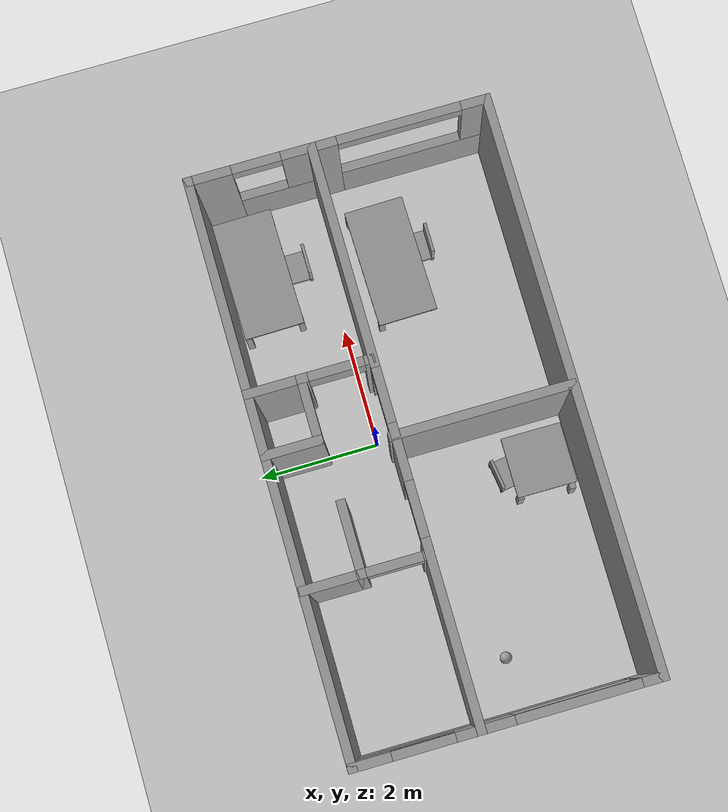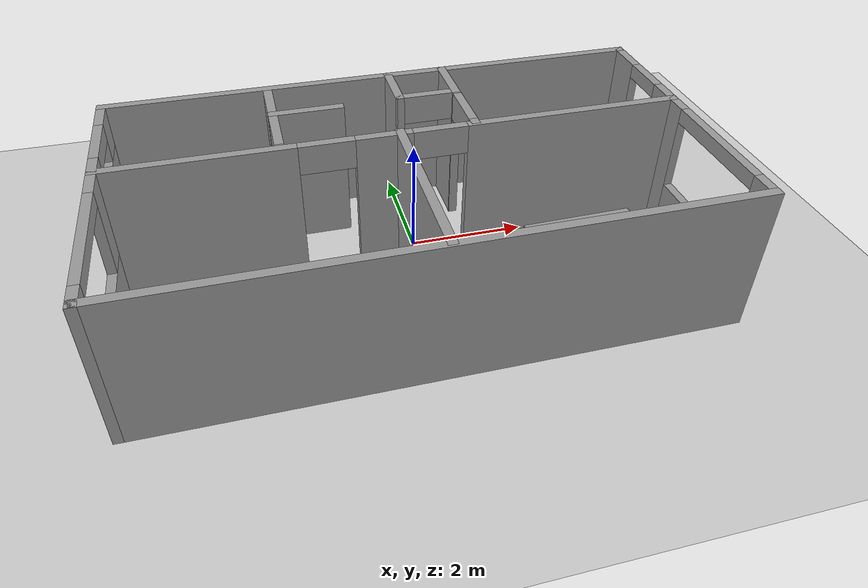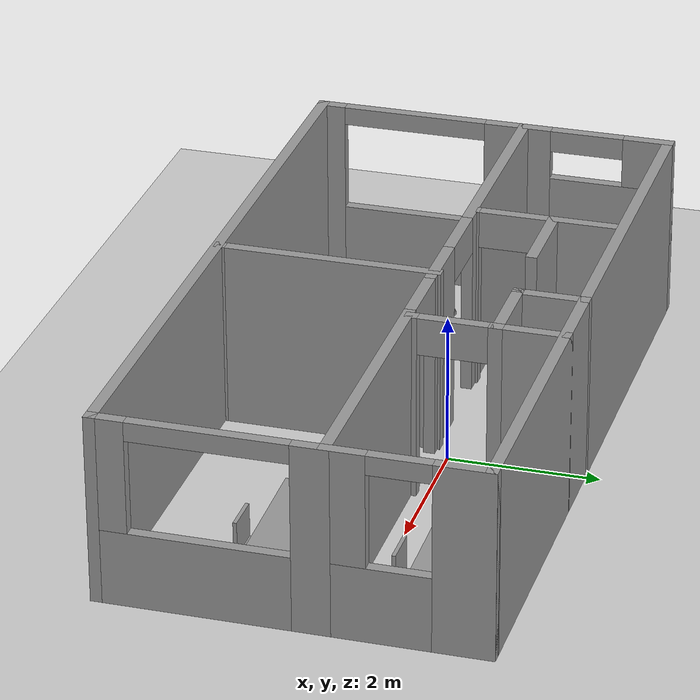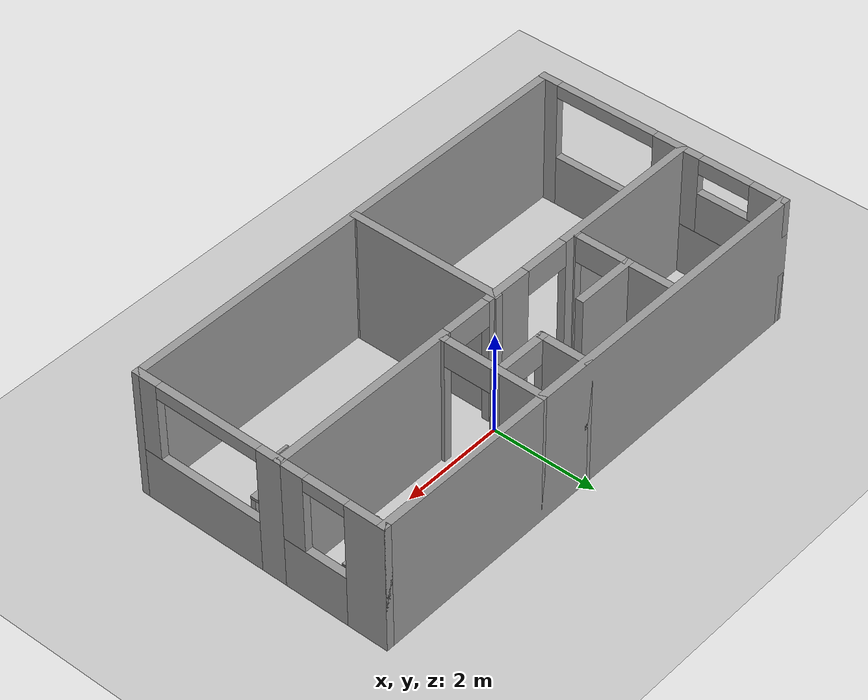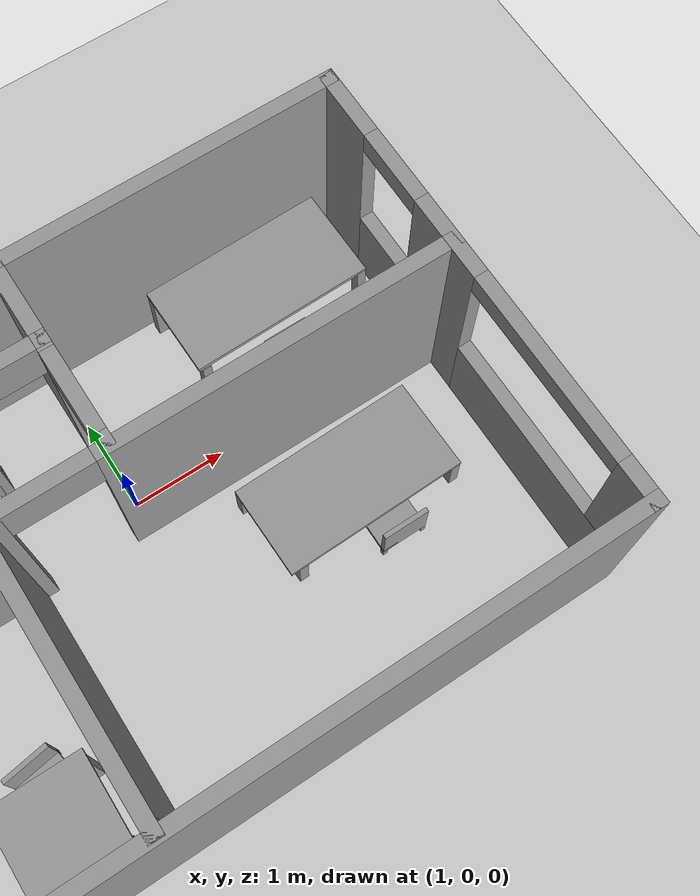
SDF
<sdf version="1.6">
 <world name="default">
  <light name="sun" type="directional">
   <pose>0 0 10 0 -0 0</pose>
   <diffuse>0.8 0.8 0.8 1</diffuse>
   <specular>0.2 0.2 0.2 1</specular>
   <attenuation>
    <range>1000</range>
    <constant>0.9</constant>
    <linear>0.01</linear>
    <quadratic>0.001</quadratic>
   </attenuation>
   <direction>-0.5 0.1 -0.9</direction>
  </light>
  <model name="ground_plane">
   <static>1</static>
   <link name="link">
    <collision name="collision">
     <geometry><plane><normal>0 0 1</normal><size>100 100</size></plane></geometry>
     <surface><friction><ode><mu>100</mu><mu2>50</mu2></ode></friction></surface>
    </collision>
    <visual name="visual">
     <cast_shadows>0</cast_shadows>
     <geometry><plane><normal>0 0 1</normal><size>100 100</size></plane></geometry>
     <material>
      <script><uri>file://media/materials/scripts/gazebo.material</uri><name>Gazebo/Grey</name></script>
     </material>
    </visual>
   </link>
  </model>
  <gravity>0 0 -9.8</gravity>
  <magnetic_field>6e-06 2.3e-05 -4.2e-05</magnetic_field>
  <atmosphere type="adiabatic"/>
  <physics name="default_physics" default="0" type="ode">
   <max_step_size>0.001</max_step_size>
   <real_time_factor>1</real_time_factor>
   <real_time_update_rate>1000</real_time_update_rate>
  </physics>
  <scene><ambient>0.4 0.4 0.4 1</ambient><background>0.7 0.7 0.7 1</background><shadows>1</shadows></scene>
  <spherical_coordinates>
   <surface_model>EARTH_WGS84</surface_model>
   <latitude_deg>0</latitude_deg>
   <longitude_deg>0</longitude_deg>
   <elevation>0</elevation>
   <heading_deg>0</heading_deg>
  </spherical_coordinates>
  <model name="1stfloor">
   <pose>-0.226451 -0.689234 0 0 -0 0</pose>
   <link name="Wall_0">
    <pose>0 0.425 0 0 -0 0</pose>
    <visual name="Wall_0_Visual_0">
     <pose>-3.21576 0 1.25 0 -0 0</pose>
     <geometry><box><size>3.06848 0.15 2.5</size></box></geometry>
     <material>
      <script><uri>file://media/materials/scripts/gazebo.material</uri><name>Gazebo/Grey</name></script>
      <ambient>1 1 1 1</ambient>
     </material>
     <meta><layer>0</layer></meta>
    </visual>
    <collision name="Wall_0_Collision_0">
     <geometry><box><size>3.06848 0.15 2.5</size></box></geometry>
     <pose>-3.21576 0 1.25 0 -0 0</pose>
    </collision>
    <visual name="Wall_0_Visual_1">
     <pose>-0.318478 0 1.25 0 -0 0</pose>
     <geometry><box><size>0.926087 0.15 2.5</size></box></geometry>
     <material>
      <script><uri>file://media/materials/scripts/gazebo.material</uri><name>Gazebo/Grey</name></script>
      <ambient>1 1 1 1</ambient>
     </material>
     <meta><layer>0</layer></meta>
    </visual>
    <collision name="Wall_0_Collision_1">
     <geometry><box><size>0.926087 0.15 2.5</size></box></geometry>
     <pose>-0.318478 0 1.25 0 -0 0</pose>
    </collision>
    <visual name="Wall_0_Visual_2">
     <pose>2.89728 0 1.25 0 -0 0</pose>
     <geometry><box><size>3.70544 0.15 2.5</size></box></geometry>
     <material>
      <script><uri>file://media/materials/scripts/gazebo.material</uri><name>Gazebo/Grey</name></script>
      <ambient>1 1 1 1</ambient>
     </material>
     <meta><layer>0</layer></meta>
    </visual>
    <collision name="Wall_0_Collision_2">
     <geometry><box><size>3.70544 0.15 2.5</size></box></geometry>
     <pose>2.89728 0 1.25 0 -0 0</pose>
    </collision>
    <visual name="Wall_0_Visual_3">
     <pose>-1.23152 0 2.25 0 -0 0</pose>
     <geometry><box><size>0.9 0.15 0.5</size></box></geometry>
     <material>
      <script><uri>file://media/materials/scripts/gazebo.material</uri><name>Gazebo/Grey</name></script>
      <ambient>1 1 1 1</ambient>
     </material>
     <meta><layer>0</layer></meta>
    </visual>
    <collision name="Wall_0_Collision_3">
     <geometry><box><size>0.9 0.15 0.5</size></box></geometry>
     <pose>-1.23152 0 2.25 0 -0 0</pose>
    </collision>
    <visual name="Wall_0_Visual_4">
     <pose>0.594565 0 2.25 0 -0 0</pose>
     <geometry><box><size>0.9 0.15 0.5</size></box></geometry>
     <material>
      <script><uri>file://media/materials/scripts/gazebo.material</uri><name>Gazebo/Grey</name></script>
      <ambient>1 1 1 1</ambient>
     </material>
     <meta><layer>0</layer></meta>
    </visual>
    <collision name="Wall_0_Collision_4">
     <geometry><box><size>0.9 0.15 0.5</size></box></geometry>
     <pose>0.594565 0 2.25 0 -0 0</pose>
    </collision>
   </link>
   <link name="Wall_1">
    <pose>4.675 -1 0 0 0 -1.5708</pose>
    <visual name="Wall_1_Visual_0">
     <pose>-1.2588 0 1.25 0 -0 0</pose>
     <geometry><box><size>0.482391 0.15 2.5</size></box></geometry>
     <material>
      <script><uri>file://media/materials/scripts/gazebo.material</uri><name>Gazebo/Grey</name></script>
      <ambient>1 1 1 1</ambient>
     </material>
     <meta><layer>0</layer></meta>
    </visual>
    <collision name="Wall_1_Collision_0">
     <geometry><box><size>0.482391 0.15 2.5</size></box></geometry>
     <pose>-1.2588 0 1.25 0 -0 0</pose>
    </collision>
    <visual name="Wall_1_Visual_1">
     <pose>0.241196 0 0.5 0 -0 0</pose>
     <geometry><box><size>2.51761 0.15 1</size></box></geometry>
     <material>
      <script><uri>file://media/materials/scripts/gazebo.material</uri><name>Gazebo/Grey</name></script>
      <ambient>1 1 1 1</ambient>
     </material>
     <meta><layer>0</layer></meta>
    </visual>
    <collision name="Wall_1_Collision_1">
     <geometry><box><size>2.51761 0.15 1</size></box></geometry>
     <pose>0.241196 0 0.5 0 -0 0</pose>
    </collision>
    <visual name="Wall_1_Visual_2">
     <pose>1.2512 0 1.75 0 -0 0</pose>
     <geometry><box><size>0.497609 0.15 1.5</size></box></geometry>
     <material>
      <script><uri>file://media/materials/scripts/gazebo.material</uri><name>Gazebo/Grey</name></script>
      <ambient>1 1 1 1</ambient>
     </material>
     <meta><layer>0</layer></meta>
    </visual>
    <collision name="Wall_1_Collision_2">
     <geometry><box><size>0.497609 0.15 1.5</size></box></geometry>
     <pose>1.2512 0 1.75 0 -0 0</pose>
    </collision>
    <visual name="Wall_1_Visual_3">
     <pose>-0.007609 0 2.375 0 -0 0</pose>
     <geometry><box><size>2.02 0.15 0.25</size></box></geometry>
     <material>
      <script><uri>file://media/materials/scripts/gazebo.material</uri><name>Gazebo/Grey</name></script>
      <ambient>1 1 1 1</ambient>
     </material>
     <meta><layer>0</layer></meta>
    </visual>
    <collision name="Wall_1_Collision_3">
     <geometry><box><size>2.02 0.15 0.25</size></box></geometry>
     <pose>-0.007609 0 2.375 0 -0 0</pose>
    </collision>
   </link>
   <link name="Wall_10">
    <collision name="Wall_10_Collision">
     <geometry><box><size>3 0.15 2.5</size></box></geometry>
     <pose>0 0 1.25 0 -0 0</pose>
    </collision>
    <visual name="Wall_10_Visual">
     <pose>0 0 1.25 0 -0 0</pose>
     <geometry><box><size>3 0.15 2.5</size></box></geometry>
     <material>
      <script><uri>file://media/materials/scripts/gazebo.material</uri><name>Gazebo/Grey</name></script>
      <ambient>1 1 1 1</ambient>
     </material>
     <meta><layer>0</layer></meta>
    </visual>
    <pose>-0.048913 -0.965217 0 0 0 -1.5708</pose>
   </link>
   <link name="Wall_11">
    <collision name="Wall_11_Collision">
     <geometry><box><size>0.15 0.15 2.5</size></box></geometry>
     <pose>0 0 1.25 0 -0 0</pose>
    </collision>
    <visual name="Wall_11_Visual">
     <pose>0 0 1.25 0 -0 0</pose>
     <geometry><box><size>0.15 0.15 2.5</size></box></geometry>
     <material>
      <script><uri>file://media/materials/scripts/gazebo.material</uri><name>Gazebo/Grey</name></script>
      <ambient>1 1 1 1</ambient>
     </material>
     <meta><layer>0</layer></meta>
    </visual>
    <pose>-0.048913 -2.39022 0 0 -0 0</pose>
   </link>
   <link name="Wall_13">
    <pose>-1.94457 1.48261 0 0 0 -1.5708</pose>
    <visual name="Wall_13_Visual_0">
     <pose>-0.474457 0 1.25 0 -0 0</pose>
     <geometry><box><size>1.05109 0.15 2.5</size></box></geometry>
     <material>
      <script><uri>file://media/materials/scripts/gazebo.material</uri><name>Gazebo/Grey</name></script>
      <ambient>1 1 1 1</ambient>
     </material>
     <meta><layer>0</layer></meta>
    </visual>
    <collision name="Wall_13_Collision_0">
     <geometry><box><size>1.05109 0.15 2.5</size></box></geometry>
     <pose>-0.474457 0 1.25 0 -0 0</pose>
    </collision>
    <visual name="Wall_13_Visual_1">
     <pose>0.975543 0 1.25 0 -0 0</pose>
     <geometry><box><size>0.048913 0.15 2.5</size></box></geometry>
     <material>
      <script><uri>file://media/materials/scripts/gazebo.material</uri><name>Gazebo/Grey</name></script>
      <ambient>1 1 1 1</ambient>
     </material>
     <meta><layer>0</layer></meta>
    </visual>
    <collision name="Wall_13_Collision_1">
     <geometry><box><size>0.048913 0.15 2.5</size></box></geometry>
     <pose>0.975543 0 1.25 0 -0 0</pose>
    </collision>
    <visual name="Wall_13_Visual_2">
     <pose>0.501087 0 2.25 0 -0 0</pose>
     <geometry><box><size>0.9 0.15 0.5</size></box></geometry>
     <material>
      <script><uri>file://media/materials/scripts/gazebo.material</uri><name>Gazebo/Grey</name></script>
      <ambient>1 1 1 1</ambient>
     </material>
     <meta><layer>0</layer></meta>
    </visual>
    <collision name="Wall_13_Collision_2">
     <geometry><box><size>0.9 0.15 0.5</size></box></geometry>
     <pose>0.501087 0 2.25 0 -0 0</pose>
    </collision>
   </link>
   <link name="Wall_15">
    <collision name="Wall_15_Collision">
     <geometry><box><size>1 0.15 2.5</size></box></geometry>
     <pose>0 0 1.25 0 -0 0</pose>
    </collision>
    <visual name="Wall_15_Visual">
     <pose>0 0 1.25 0 -0 0</pose>
     <geometry><box><size>1 0.15 2.5</size></box></geometry>
     <material>
      <script><uri>file://media/materials/scripts/gazebo.material</uri><name>Gazebo/Grey</name></script>
      <ambient>1 1 1 1</ambient>
     </material>
     <meta><layer>0</layer></meta>
    </visual>
    <pose>0.194565 2 0 0 0 -1.5708</pose>
   </link>
   <link name="Wall_17">
    <collision name="Wall_17_Collision">
     <geometry><box><size>1 0.15 2.5</size></box></geometry>
     <pose>0 0 1.25 0 -0 0</pose>
    </collision>
    <visual name="Wall_17_Visual">
     <pose>0 0 1.25 0 -0 0</pose>
     <geometry><box><size>1 0.15 2.5</size></box></geometry>
     <material>
      <script><uri>file://media/materials/scripts/gazebo.material</uri><name>Gazebo/Grey</name></script>
      <ambient>1 1 1 1</ambient>
     </material>
     <meta><layer>0</layer></meta>
    </visual>
    <pose>1.18587 2 0 0 0 -1.5708</pose>
   </link>
   <link name="Wall_18">
    <pose>0.690217 1.575 0 0 -0 3.14159</pose>
    <visual name="Wall_18_Visual_0">
     <pose>-0.497283 0 1.25 0 -0 0</pose>
     <geometry><box><size>0.146739 0.15 2.5</size></box></geometry>
     <material>
      <script><uri>file://media/materials/scripts/gazebo.material</uri><name>Gazebo/Grey</name></script>
      <ambient>1 1 1 1</ambient>
     </material>
     <meta><layer>0</layer></meta>
    </visual>
    <collision name="Wall_18_Collision_0">
     <geometry><box><size>0.146739 0.15 2.5</size></box></geometry>
     <pose>-0.497283 0 1.25 0 -0 0</pose>
    </collision>
    <visual name="Wall_18_Visual_1">
     <pose>0.52337 0 1.25 0 -0 0</pose>
     <geometry><box><size>0.094565 0.15 2.5</size></box></geometry>
     <material>
      <script><uri>file://media/materials/scripts/gazebo.material</uri><name>Gazebo/Grey</name></script>
      <ambient>1 1 1 1</ambient>
     </material>
     <meta><layer>0</layer></meta>
    </visual>
    <collision name="Wall_18_Collision_1">
     <geometry><box><size>0.094565 0.15 2.5</size></box></geometry>
     <pose>0.52337 0 1.25 0 -0 0</pose>
    </collision>
    <visual name="Wall_18_Visual_2">
     <pose>0.026087 0 2.25 0 -0 0</pose>
     <geometry><box><size>0.9 0.15 0.5</size></box></geometry>
     <material>
      <script><uri>file://media/materials/scripts/gazebo.material</uri><name>Gazebo/Grey</name></script>
      <ambient>1 1 1 1</ambient>
     </material>
     <meta><layer>0</layer></meta>
    </visual>
    <collision name="Wall_18_Collision_2">
     <geometry><box><size>0.9 0.15 0.5</size></box></geometry>
     <pose>0.026087 0 2.25 0 -0 0</pose>
    </collision>
   </link>
   <link name="Wall_19">
    <collision name="Wall_19_Collision">
     <geometry><box><size>0.15 0.15 2.5</size></box></geometry>
     <pose>0 0 1.25 0 -0 0</pose>
    </collision>
    <visual name="Wall_19_Visual">
     <pose>0 0 1.25 0 -0 0</pose>
     <geometry><box><size>0.15 0.15 2.5</size></box></geometry>
     <material>
      <script><uri>file://media/materials/scripts/gazebo.material</uri><name>Gazebo/Grey</name></script>
      <ambient>1 1 1 1</ambient>
     </material>
     <meta><layer>0</layer></meta>
    </visual>
    <pose>0.194565 1.575 0 0 -0 0</pose>
   </link>
   <link name="Wall_2">
    <collision name="Wall_2_Collision">
     <geometry><box><size>9.5 0.15 2.5</size></box></geometry>
     <pose>0 0 1.25 0 -0 0</pose>
    </collision>
    <visual name="Wall_2_Visual">
     <pose>0 0 1.25 0 -0 0</pose>
     <geometry><box><size>9.5 0.15 2.5</size></box></geometry>
     <material>
      <script><uri>file://media/materials/scripts/gazebo.material</uri><name>Gazebo/Grey</name></script>
      <ambient>1 1 1 1</ambient>
     </material>
     <meta><layer>0</layer></meta>
    </visual>
    <pose>0 -2.425 0 0 -0 3.14159</pose>
   </link>
   <link name="Wall_21">
    <pose>1.18587 1.025 0 0 0 -1.5708</pose>
    <visual name="Wall_21_Visual_0">
     <pose>-0.533152 0 1.25 0 -0 0</pose>
     <geometry><box><size>0.183696 0.15 2.5</size></box></geometry>
     <material>
      <script><uri>file://media/materials/scripts/gazebo.material</uri><name>Gazebo/Grey</name></script>
      <ambient>1 1 1 1</ambient>
     </material>
     <meta><layer>0</layer></meta>
    </visual>
    <collision name="Wall_21_Collision_0">
     <geometry><box><size>0.183696 0.15 2.5</size></box></geometry>
     <pose>-0.533152 0 1.25 0 -0 0</pose>
    </collision>
    <visual name="Wall_21_Visual_1">
     <pose>0.541848 0 1.25 0 -0 0</pose>
     <geometry><box><size>0.166304 0.15 2.5</size></box></geometry>
     <material>
      <script><uri>file://media/materials/scripts/gazebo.material</uri><name>Gazebo/Grey</name></script>
      <ambient>1 1 1 1</ambient>
     </material>
     <meta><layer>0</layer></meta>
    </visual>
    <collision name="Wall_21_Collision_1">
     <geometry><box><size>0.166304 0.15 2.5</size></box></geometry>
     <pose>0.541848 0 1.25 0 -0 0</pose>
    </collision>
    <visual name="Wall_21_Visual_2">
     <pose>0.008696 0 2.25 0 -0 0</pose>
     <geometry><box><size>0.9 0.15 0.5</size></box></geometry>
     <material>
      <script><uri>file://media/materials/scripts/gazebo.material</uri><name>Gazebo/Grey</name></script>
      <ambient>1 1 1 1</ambient>
     </material>
     <meta><layer>0</layer></meta>
    </visual>
    <collision name="Wall_21_Collision_2">
     <geometry><box><size>0.9 0.15 0.5</size></box></geometry>
     <pose>0.008696 0 2.25 0 -0 0</pose>
    </collision>
   </link>
   <link name="Wall_23">
    <collision name="Wall_23_Collision">
     <geometry><box><size>1.25 0.15 2.5</size></box></geometry>
     <pose>0 0 1.25 0 -0 0</pose>
    </collision>
    <visual name="Wall_23_Visual">
     <pose>0 0 1.25 0 -0 0</pose>
     <geometry><box><size>1.25 0.15 2.5</size></box></geometry>
     <material>
      <script><uri>file://media/materials/scripts/gazebo.material</uri><name>Gazebo/Grey</name></script>
      <ambient>1 1 1 1</ambient>
     </material>
     <meta><layer>0</layer></meta>
    </visual>
    <pose>-1.39457 1.50326 0 0 -0 0</pose>
   </link>
   <link name="Wall_3">
    <pose>-4.675 0 0 0 -0 1.5708</pose>
    <visual name="Wall_3_Visual_0">
     <pose>-2.29772 0 1.25 0 -0 0</pose>
     <geometry><box><size>0.404565 0.15 2.5</size></box></geometry>
     <material>
      <script><uri>file://media/materials/scripts/gazebo.material</uri><name>Gazebo/Grey</name></script>
      <ambient>1 1 1 1</ambient>
     </material>
     <meta><layer>0</layer></meta>
    </visual>
    <collision name="Wall_3_Collision_0">
     <geometry><box><size>0.404565 0.15 2.5</size></box></geometry>
     <pose>-2.29772 0 1.25 0 -0 0</pose>
    </collision>
    <visual name="Wall_3_Visual_1">
     <pose>0.202283 0 0.5 0 -0 0</pose>
     <geometry><box><size>4.59544 0.15 1</size></box></geometry>
     <material>
      <script><uri>file://media/materials/scripts/gazebo.material</uri><name>Gazebo/Grey</name></script>
      <ambient>1 1 1 1</ambient>
     </material>
     <meta><layer>0</layer></meta>
    </visual>
    <collision name="Wall_3_Collision_1">
     <geometry><box><size>4.59544 0.15 1</size></box></geometry>
     <pose>0.202283 0 0.5 0 -0 0</pose>
    </collision>
    <visual name="Wall_3_Visual_2">
     <pose>0.348261 0 1.75 0 -0 0</pose>
     <geometry><box><size>0.927391 0.15 1.5</size></box></geometry>
     <material>
      <script><uri>file://media/materials/scripts/gazebo.material</uri><name>Gazebo/Grey</name></script>
      <ambient>1 1 1 1</ambient>
     </material>
     <meta><layer>0</layer></meta>
    </visual>
    <collision name="Wall_3_Collision_2">
     <geometry><box><size>0.927391 0.15 1.5</size></box></geometry>
     <pose>0.348261 0 1.75 0 -0 0</pose>
    </collision>
    <visual name="Wall_3_Visual_3">
     <pose>1.65598 0 1.4 0 -0 0</pose>
     <geometry><box><size>1.68804 0.15 0.8</size></box></geometry>
     <material>
      <script><uri>file://media/materials/scripts/gazebo.material</uri><name>Gazebo/Grey</name></script>
      <ambient>1 1 1 1</ambient>
     </material>
     <meta><layer>0</layer></meta>
    </visual>
    <collision name="Wall_3_Collision_3">
     <geometry><box><size>1.68804 0.15 0.8</size></box></geometry>
     <pose>1.65598 0 1.4 0 -0 0</pose>
    </collision>
    <visual name="Wall_3_Visual_4">
     <pose>2.15598 0 2.15 0 -0 0</pose>
     <geometry><box><size>0.688044 0.15 0.7</size></box></geometry>
     <material>
      <script><uri>file://media/materials/scripts/gazebo.material</uri><name>Gazebo/Grey</name></script>
      <ambient>1 1 1 1</ambient>
     </material>
     <meta><layer>0</layer></meta>
    </visual>
    <collision name="Wall_3_Collision_4">
     <geometry><box><size>0.688044 0.15 0.7</size></box></geometry>
     <pose>2.15598 0 2.15 0 -0 0</pose>
    </collision>
    <visual name="Wall_3_Visual_5">
     <pose>1.31196 0 2.35 0 -0 0</pose>
     <geometry><box><size>1 0.15 0.3</size></box></geometry>
     <material>
      <script><uri>file://media/materials/scripts/gazebo.material</uri><name>Gazebo/Grey</name></script>
      <ambient>1 1 1 1</ambient>
     </material>
     <meta><layer>0</layer></meta>
    </visual>
    <collision name="Wall_3_Collision_5">
     <geometry><box><size>1 0.15 0.3</size></box></geometry>
     <pose>1.31196 0 2.35 0 -0 0</pose>
    </collision>
    <visual name="Wall_3_Visual_6">
     <pose>-1.10543 0 2.375 0 -0 0</pose>
     <geometry><box><size>1.98 0.15 0.25</size></box></geometry>
     <material>
      <script><uri>file://media/materials/scripts/gazebo.material</uri><name>Gazebo/Grey</name></script>
      <ambient>1 1 1 1</ambient>
     </material>
     <meta><layer>0</layer></meta>
    </visual>
    <collision name="Wall_3_Collision_6">
     <geometry><box><size>1.98 0.15 0.25</size></box></geometry>
     <pose>-1.10543 0 2.375 0 -0 0</pose>
    </collision>
   </link>
   <link name="Wall_4">
    <collision name="Wall_4_Collision">
     <geometry><box><size>9.5 0.15 2.5</size></box></geometry>
     <pose>0 0 1.25 0 -0 0</pose>
    </collision>
    <visual name="Wall_4_Visual">
     <pose>0 0 1.25 0 -0 0</pose>
     <geometry><box><size>9.5 0.15 2.5</size></box></geometry>
     <material>
      <script><uri>file://media/materials/scripts/gazebo.material</uri><name>Gazebo/Grey</name></script>
      <ambient>1 1 1 1</ambient>
     </material>
     <meta><layer>0</layer></meta>
    </visual>
    <pose>0 2.425 0 0 -0 0</pose>
   </link>
   <link name="Wall_5">
    <collision name="Wall_5_Collision">
     <geometry><box><size>0.15 0.15 2.5</size></box></geometry>
     <pose>0 0 1.25 0 -0 0</pose>
    </collision>
    <visual name="Wall_5_Visual">
     <pose>0 0 1.25 0 -0 0</pose>
     <geometry><box><size>0.15 0.15 2.5</size></box></geometry>
     <material>
      <script><uri>file://media/materials/scripts/gazebo.material</uri><name>Gazebo/Grey</name></script>
      <ambient>1 1 1 1</ambient>
     </material>
     <meta><layer>0</layer></meta>
    </visual>
    <pose>4.675 2.425 0 0 -0 0</pose>
   </link>
   <link name="Wall_7">
    <pose>4.675 1.425 0 0 0 -1.5708</pose>
    <visual name="Wall_7_Visual_0">
     <pose>-0.689674 0 1.25 0 -0 0</pose>
     <geometry><box><size>0.770652 0.15 2.5</size></box></geometry>
     <material>
      <script><uri>file://media/materials/scripts/gazebo.material</uri><name>Gazebo/Grey</name></script>
      <ambient>1 1 1 1</ambient>
     </material>
     <meta><layer>0</layer></meta>
    </visual>
    <collision name="Wall_7_Collision_0">
     <geometry><box><size>0.770652 0.15 2.5</size></box></geometry>
     <pose>-0.689674 0 1.25 0 -0 0</pose>
    </collision>
    <visual name="Wall_7_Visual_1">
     <pose>0.385326 0 0.5 0 -0 0</pose>
     <geometry><box><size>1.37935 0.15 1</size></box></geometry>
     <material>
      <script><uri>file://media/materials/scripts/gazebo.material</uri><name>Gazebo/Grey</name></script>
      <ambient>1 1 1 1</ambient>
     </material>
     <meta><layer>0</layer></meta>
    </visual>
    <collision name="Wall_7_Collision_1">
     <geometry><box><size>1.37935 0.15 1</size></box></geometry>
     <pose>0.385326 0 0.5 0 -0 0</pose>
    </collision>
    <visual name="Wall_7_Visual_2">
     <pose>0.785326 0 1.75 0 -0 0</pose>
     <geometry><box><size>0.579348 0.15 1.5</size></box></geometry>
     <material>
      <script><uri>file://media/materials/scripts/gazebo.material</uri><name>Gazebo/Grey</name></script>
      <ambient>1 1 1 1</ambient>
     </material>
     <meta><layer>0</layer></meta>
    </visual>
    <collision name="Wall_7_Collision_2">
     <geometry><box><size>0.579348 0.15 1.5</size></box></geometry>
     <pose>0.785326 0 1.75 0 -0 0</pose>
    </collision>
    <visual name="Wall_7_Visual_3">
     <pose>0.095652 0 2.375 0 -0 0</pose>
     <geometry><box><size>0.8 0.15 0.25</size></box></geometry>
     <material>
      <script><uri>file://media/materials/scripts/gazebo.material</uri><name>Gazebo/Grey</name></script>
      <ambient>1 1 1 1</ambient>
     </material>
     <meta><layer>0</layer></meta>
    </visual>
    <collision name="Wall_7_Collision_3">
     <geometry><box><size>0.8 0.15 0.25</size></box></geometry>
     <pose>0.095652 0 2.375 0 -0 0</pose>
    </collision>
   </link>
   <link name="Wall_8">
    <collision name="Wall_8_Collision">
     <geometry><box><size>0.15 0.15 2.5</size></box></geometry>
     <pose>0 0 1.25 0 -0 0</pose>
    </collision>
    <visual name="Wall_8_Visual">
     <pose>0 0 1.25 0 -0 0</pose>
     <geometry><box><size>0.15 0.15 2.5</size></box></geometry>
     <material>
      <script><uri>file://media/materials/scripts/gazebo.material</uri><name>Gazebo/Grey</name></script>
      <ambient>1 1 1 1</ambient>
     </material>
     <meta><layer>0</layer></meta>
    </visual>
    <pose>4.675 0.425 0 0 -0 0</pose>
   </link>
   <static>1</static>
  </model>
  <model name="table">
   <link name="link_2">
    <pose>-0.000914 0.01077 -0.287764 0 -0 0</pose>
    <inertial>
     <mass>1</mass>
     <inertia>
      <ixx>0.166667</ixx>
      <ixy>0</ixy>
      <ixz>0</ixz>
      <iyy>0.166667</iyy>
      <iyz>0</iyz>
      <izz>0.166667</izz>
     </inertia>
    </inertial>
    <visual name="visual">
     <pose>0 0 0.75 0 -0 0</pose>
     <geometry><box><size>1 1 0.05</size></box></geometry>
     <material>
      <lighting>1</lighting>
      <script><uri>file://media/materials/scripts/gazebo.material</uri><name>Gazebo/Grey</name></script>
      <ambient>0.3 0.3 0.3 1</ambient>
      <diffuse>0.7 0.7 0.7 1</diffuse>
      <specular>0.01 0.01 0.01 1</specular>
      <emissive>0 0 0 1</emissive>
      <shader type="vertex"><normal_map>__default__</normal_map></shader>
     </material>
    </visual>
    <collision name="collision">
     <pose>0 0 0.75 0 -0 0</pose>
     <geometry><box><size>1 1 0.05</size></box></geometry>
     <surface>
      <friction>
       <ode><mu>1</mu><mu2>1</mu2><fdir1>0 0 0</fdir1><slip1>0</slip1><slip2>0</slip2></ode>
       <torsional>
        <coefficient>1</coefficient>
        <patch_radius>0</patch_radius>
        <surface_radius>0</surface_radius>
        <use_patch_radius>1</use_patch_radius>
        <ode><slip>0</slip></ode>
       </torsional>
      </friction>
      <bounce><restitution_coefficient>0</restitution_coefficient><threshold>1e+06</threshold></bounce>
      <contact>
       <collide_without_contact>0</collide_without_contact>
       <collide_without_contact_bitmask>1</collide_without_contact_bitmask>
       <collide_bitmask>1</collide_bitmask>
       <ode>
        <soft_cfm>0</soft_cfm>
        <soft_erp>0.2</soft_erp>
        <kp>1e+13</kp>
        <kd>1</kd>
        <max_vel>0.01</max_vel>
        <min_depth>0</min_depth>
       </ode>
       <bullet>
        <split_impulse>1</split_impulse>
        <split_impulse_penetration_threshold>-0.01</split_impulse_penetration_threshold>
        <soft_cfm>0</soft_cfm>
        <soft_erp>0.2</soft_erp>
        <kp>1e+13</kp>
        <kd>1</kd>
       </bullet>
      </contact>
     </surface>
    </collision>
   </link>
   <link name="link_3">
    <pose>-0.483131 0.454991 0.080236 0 -0 0</pose>
    <inertial>
     <mass>1</mass>
     <inertia>
      <ixx>0.166667</ixx>
      <ixy>0</ixy>
      <ixz>0</ixz>
      <iyy>0.166667</iyy>
      <iyz>0</iyz>
      <izz>0.166667</izz>
     </inertia>
    </inertial>
    <visual name="visual">
     <geometry><box><size>0.1 0.1 0.75</size></box></geometry>
     <material>
      <lighting>1</lighting>
      <script><uri>file://media/materials/scripts/gazebo.material</uri><name>Gazebo/Grey</name></script>
      <ambient>0.3 0.3 0.3 1</ambient>
      <diffuse>0.7 0.7 0.7 1</diffuse>
      <specular>0.01 0.01 0.01 1</specular>
      <emissive>0 0 0 1</emissive>
      <shader type="vertex"><normal_map>__default__</normal_map></shader>
     </material>
    </visual>
    <collision name="collision">
     <geometry><box><size>0.1 0.1 0.75</size></box></geometry>
     <surface>
      <friction>
       <ode><mu>1</mu><mu2>1</mu2><fdir1>0 0 0</fdir1><slip1>0</slip1><slip2>0</slip2></ode>
       <torsional>
        <coefficient>1</coefficient>
        <patch_radius>0</patch_radius>
        <surface_radius>0</surface_radius>
        <use_patch_radius>1</use_patch_radius>
        <ode><slip>0</slip></ode>
       </torsional>
      </friction>
      <bounce><restitution_coefficient>0</restitution_coefficient><threshold>1e+06</threshold></bounce>
      <contact>
       <collide_without_contact>0</collide_without_contact>
       <collide_without_contact_bitmask>1</collide_without_contact_bitmask>
       <collide_bitmask>1</collide_bitmask>
       <ode>
        <soft_cfm>0</soft_cfm>
        <soft_erp>0.2</soft_erp>
        <kp>1e+13</kp>
        <kd>1</kd>
        <max_vel>0.01</max_vel>
        <min_depth>0</min_depth>
       </ode>
       <bullet>
        <split_impulse>1</split_impulse>
        <split_impulse_penetration_threshold>-0.01</split_impulse_penetration_threshold>
        <soft_cfm>0</soft_cfm>
        <soft_erp>0.2</soft_erp>
        <kp>1e+13</kp>
        <kd>1</kd>
       </bullet>
      </contact>
     </surface>
    </collision>
   </link>
   <link name="link_3_clone_0">
    <pose>0.45366 -0.416964 0.047057 0 -0 0</pose>
    <inertial>
     <mass>1</mass>
     <inertia>
      <ixx>0.166667</ixx>
      <ixy>0</ixy>
      <ixz>0</ixz>
      <iyy>0.166667</iyy>
      <iyz>0</iyz>
      <izz>0.166667</izz>
     </inertia>
    </inertial>
    <visual name="visual">
     <geometry><box><size>0.1 0.1 0.75</size></box></geometry>
     <material>
      <lighting>1</lighting>
      <script><uri>file://media/materials/scripts/gazebo.material</uri><name>Gazebo/Grey</name></script>
      <ambient>0.3 0.3 0.3 1</ambient>
      <diffuse>0.7 0.7 0.7 1</diffuse>
      <specular>0.01 0.01 0.01 1</specular>
      <emissive>0 0 0 1</emissive>
      <shader type="vertex"><normal_map>__default__</normal_map></shader>
     </material>
    </visual>
    <collision name="collision">
     <geometry><box><size>0.1 0.1 0.75</size></box></geometry>
     <surface>
      <friction>
       <ode><mu>1</mu><mu2>1</mu2><fdir1>0 0 0</fdir1><slip1>0</slip1><slip2>0</slip2></ode>
       <torsional>
        <coefficient>1</coefficient>
        <patch_radius>0</patch_radius>
        <surface_radius>0</surface_radius>
        <use_patch_radius>1</use_patch_radius>
        <ode><slip>0</slip></ode>
       </torsional>
      </friction>
      <bounce><restitution_coefficient>0</restitution_coefficient><threshold>1e+06</threshold></bounce>
      <contact>
       <collide_without_contact>0</collide_without_contact>
       <collide_without_contact_bitmask>1</collide_without_contact_bitmask>
       <collide_bitmask>1</collide_bitmask>
       <ode>
        <soft_cfm>0</soft_cfm>
        <soft_erp>0.2</soft_erp>
        <kp>1e+13</kp>
        <kd>1</kd>
        <max_vel>0.01</max_vel>
        <min_depth>0</min_depth>
       </ode>
       <bullet>
        <split_impulse>1</split_impulse>
        <split_impulse_penetration_threshold>-0.01</split_impulse_penetration_threshold>
        <soft_cfm>0</soft_cfm>
        <soft_erp>0.2</soft_erp>
        <kp>1e+13</kp>
        <kd>1</kd>
       </bullet>
      </contact>
     </surface>
    </collision>
   </link>
   <link name="link_3_clone_0_clone">
    <pose>-0.543347 -0.399935 0.089996 -0.02 -0 -0</pose>
    <inertial>
     <mass>1</mass>
     <inertia>
      <ixx>0.166667</ixx>
      <ixy>0</ixy>
      <ixz>0</ixz>
      <iyy>0.166667</iyy>
      <iyz>0</iyz>
      <izz>0.166667</izz>
     </inertia>
    </inertial>
    <visual name="visual">
     <geometry><box><size>0.1 0.1 0.75</size></box></geometry>
     <material>
      <lighting>1</lighting>
      <script><uri>file://media/materials/scripts/gazebo.material</uri><name>Gazebo/Grey</name></script>
      <ambient>0.3 0.3 0.3 1</ambient>
      <diffuse>0.7 0.7 0.7 1</diffuse>
      <specular>0.01 0.01 0.01 1</specular>
      <emissive>0 0 0 1</emissive>
      <shader type="vertex"><normal_map>__default__</normal_map></shader>
     </material>
    </visual>
    <collision name="collision">
     <geometry><box><size>0.1 0.1 0.75</size></box></geometry>
     <surface>
      <friction>
       <ode><mu>1</mu><mu2>1</mu2><fdir1>0 0 0</fdir1><slip1>0</slip1><slip2>0</slip2></ode>
       <torsional>
        <coefficient>1</coefficient>
        <patch_radius>0</patch_radius>
        <surface_radius>0</surface_radius>
        <use_patch_radius>1</use_patch_radius>
        <ode><slip>0</slip></ode>
       </torsional>
      </friction>
      <bounce><restitution_coefficient>0</restitution_coefficient><threshold>1e+06</threshold></bounce>
      <contact>
       <collide_without_contact>0</collide_without_contact>
       <collide_without_contact_bitmask>1</collide_without_contact_bitmask>
       <collide_bitmask>1</collide_bitmask>
       <ode>
        <soft_cfm>0</soft_cfm>
        <soft_erp>0.2</soft_erp>
        <kp>1e+13</kp>
        <kd>1</kd>
        <max_vel>0.01</max_vel>
        <min_depth>0</min_depth>
       </ode>
       <bullet>
        <split_impulse>1</split_impulse>
        <split_impulse_penetration_threshold>-0.01</split_impulse_penetration_threshold>
        <soft_cfm>0</soft_cfm>
        <soft_erp>0.2</soft_erp>
        <kp>1e+13</kp>
        <kd>1</kd>
       </bullet>
      </contact>
     </surface>
    </collision>
   </link>
   <link name="link_3_clone_1">
    <pose>0.449089 0.399103 0.080236 0 -0 0</pose>
    <inertial>
     <mass>1</mass>
     <inertia>
      <ixx>0.166667</ixx>
      <ixy>0</ixy>
      <ixz>0</ixz>
      <iyy>0.166667</iyy>
      <iyz>0</iyz>
      <izz>0.166667</izz>
     </inertia>
    </inertial>
    <visual name="visual">
     <geometry><box><size>0.1 0.1 0.75</size></box></geometry>
     <material>
      <lighting>1</lighting>
      <script><uri>file://media/materials/scripts/gazebo.material</uri><name>Gazebo/Grey</name></script>
      <ambient>0.3 0.3 0.3 1</ambient>
      <diffuse>0.7 0.7 0.7 1</diffuse>
      <specular>0.01 0.01 0.01 1</specular>
      <emissive>0 0 0 1</emissive>
      <shader type="vertex"><normal_map>__default__</normal_map></shader>
     </material>
    </visual>
    <collision name="collision">
     <geometry><box><size>0.1 0.1 0.75</size></box></geometry>
     <surface>
      <friction>
       <ode><mu>1</mu><mu2>1</mu2><fdir1>0 0 0</fdir1><slip1>0</slip1><slip2>0</slip2></ode>
       <torsional>
        <coefficient>1</coefficient>
        <patch_radius>0</patch_radius>
        <surface_radius>0</surface_radius>
        <use_patch_radius>1</use_patch_radius>
        <ode><slip>0</slip></ode>
       </torsional>
      </friction>
      <bounce><restitution_coefficient>0</restitution_coefficient><threshold>1e+06</threshold></bounce>
      <contact>
       <collide_without_contact>0</collide_without_contact>
       <collide_without_contact_bitmask>1</collide_without_contact_bitmask>
       <collide_bitmask>1</collide_bitmask>
       <ode>
        <soft_cfm>0</soft_cfm>
        <soft_erp>0.2</soft_erp>
        <kp>1e+13</kp>
        <kd>1</kd>
        <max_vel>0.01</max_vel>
        <min_depth>0</min_depth>
       </ode>
       <bullet>
        <split_impulse>1</split_impulse>
        <split_impulse_penetration_threshold>-0.01</split_impulse_penetration_threshold>
        <soft_cfm>0</soft_cfm>
        <soft_erp>0.2</soft_erp>
        <kp>1e+13</kp>
        <kd>1</kd>
       </bullet>
      </contact>
     </surface>
    </collision>
   </link>
   <joint name="link_2_JOINT_10" type="fixed">
    <parent>link_2</parent>
    <child>link_3_clone_1</child>
    <physics>
     <ode><limit><cfm>0</cfm><erp>0.2</erp></limit><suspension><cfm>0</cfm><erp>0.2</erp></suspension></ode>
    </physics>
   </joint>
   <joint name="link_2_JOINT_11" type="fixed">
    <parent>link_2</parent>
    <child>link_3</child>
    <physics>
     <ode><limit><cfm>0</cfm><erp>0.2</erp></limit><suspension><cfm>0</cfm><erp>0.2</erp></suspension></ode>
    </physics>
   </joint>
   <joint name="link_2_JOINT_12" type="fixed">
    <parent>link_2</parent>
    <child>link_3_clone_0_clone</child>
    <physics>
     <ode><limit><cfm>0</cfm><erp>0.2</erp></limit><suspension><cfm>0</cfm><erp>0.2</erp></suspension></ode>
    </physics>
   </joint>
   <joint name="link_2_JOINT_8" type="fixed">
    <parent>link_2</parent>
    <child>link_3_clone_0</child>
    <physics>
     <ode><limit><cfm>0</cfm><erp>0.2</erp></limit><suspension><cfm>0</cfm><erp>0.2</erp></suspension></ode>
    </physics>
   </joint>
   <joint name="link_2_JOINT_9" type="fixed">
    <parent>link_2</parent>
    <child>link_3</child>
    <physics>
     <ode><limit><cfm>0</cfm><erp>0.2</erp></limit><suspension><cfm>0</cfm><erp>0.2</erp></suspension></ode>
    </physics>
   </joint>
   <static>0</static>
   <pose>-1.07282 -2.44989 0.309674 -0.017788 -0.001792 -0.005431</pose>
  </model>
  <model name="table_0">
   <link name="link_2">
    <pose>-0.000914 0.01077 -0.287764 0 -0 0</pose>
    <inertial>
     <mass>1</mass>
     <inertia>
      <ixx>0.166667</ixx>
      <ixy>0</ixy>
      <ixz>0</ixz>
      <iyy>0.166667</iyy>
      <iyz>0</iyz>
      <izz>0.166667</izz>
     </inertia>
    </inertial>
    <visual name="visual">
     <pose>0 0 0.75 0 -0 0</pose>
     <geometry><box><size>1 2 0.05</size></box></geometry>
     <material>
      <lighting>1</lighting>
      <script><uri>file://media/materials/scripts/gazebo.material</uri><name>Gazebo/Grey</name></script>
      <ambient>0.3 0.3 0.3 1</ambient>
      <diffuse>0.7 0.7 0.7 1</diffuse>
      <specular>0.01 0.01 0.01 1</specular>
      <emissive>0 0 0 1</emissive>
      <shader type="vertex"><normal_map>__default__</normal_map></shader>
     </material>
    </visual>
    <collision name="collision">
     <pose>0 0 0.75 0 -0 0</pose>
     <geometry><box><size>1 2 0.05</size></box></geometry>
     <surface>
      <friction>
       <ode><mu>1</mu><mu2>1</mu2><fdir1>0 0 0</fdir1><slip1>0</slip1><slip2>0</slip2></ode>
       <torsional>
        <coefficient>1</coefficient>
        <patch_radius>0</patch_radius>
        <surface_radius>0</surface_radius>
        <use_patch_radius>1</use_patch_radius>
        <ode><slip>0</slip></ode>
       </torsional>
      </friction>
      <bounce><restitution_coefficient>0</restitution_coefficient><threshold>1e+06</threshold></bounce>
      <contact>
       <collide_without_contact>0</collide_without_contact>
       <collide_without_contact_bitmask>1</collide_without_contact_bitmask>
       <collide_bitmask>1</collide_bitmask>
       <ode>
        <soft_cfm>0</soft_cfm>
        <soft_erp>0.2</soft_erp>
        <kp>1e+13</kp>
        <kd>1</kd>
        <max_vel>0.01</max_vel>
        <min_depth>0</min_depth>
       </ode>
       <bullet>
        <split_impulse>1</split_impulse>
        <split_impulse_penetration_threshold>-0.01</split_impulse_penetration_threshold>
        <soft_cfm>0</soft_cfm>
        <soft_erp>0.2</soft_erp>
        <kp>1e+13</kp>
        <kd>1</kd>
       </bullet>
      </contact>
     </surface>
    </collision>
   </link>
   <link name="link_3">
    <pose>-0.450914 0.87078 0.080236 0 -0 0</pose>
    <inertial>
     <mass>1</mass>
     <inertia>
      <ixx>0.166667</ixx>
      <ixy>0</ixy>
      <ixz>0</ixz>
      <iyy>0.166667</iyy>
      <iyz>0</iyz>
      <izz>0.166667</izz>
     </inertia>
    </inertial>
    <visual name="visual">
     <geometry><box><size>0.1 0.1 0.75</size></box></geometry>
     <material>
      <lighting>1</lighting>
      <script><uri>file://media/materials/scripts/gazebo.material</uri><name>Gazebo/Grey</name></script>
      <ambient>0.3 0.3 0.3 1</ambient>
      <diffuse>0.7 0.7 0.7 1</diffuse>
      <specular>0.01 0.01 0.01 1</specular>
      <emissive>0 0 0 1</emissive>
      <shader type="vertex"><normal_map>__default__</normal_map></shader>
     </material>
    </visual>
    <collision name="collision">
     <geometry><box><size>0.1 0.1 0.75</size></box></geometry>
     <surface>
      <friction>
       <ode><mu>1</mu><mu2>1</mu2><fdir1>0 0 0</fdir1><slip1>0</slip1><slip2>0</slip2></ode>
       <torsional>
        <coefficient>1</coefficient>
        <patch_radius>0</patch_radius>
        <surface_radius>0</surface_radius>
        <use_patch_radius>1</use_patch_radius>
        <ode><slip>0</slip></ode>
       </torsional>
      </friction>
      <bounce><restitution_coefficient>0</restitution_coefficient><threshold>1e+06</threshold></bounce>
      <contact>
       <collide_without_contact>0</collide_without_contact>
       <collide_without_contact_bitmask>1</collide_without_contact_bitmask>
       <collide_bitmask>1</collide_bitmask>
       <ode>
        <soft_cfm>0</soft_cfm>
        <soft_erp>0.2</soft_erp>
        <kp>1e+13</kp>
        <kd>1</kd>
        <max_vel>0.01</max_vel>
        <min_depth>0</min_depth>
       </ode>
       <bullet>
        <split_impulse>1</split_impulse>
        <split_impulse_penetration_threshold>-0.01</split_impulse_penetration_threshold>
        <soft_cfm>0</soft_cfm>
        <soft_erp>0.2</soft_erp>
        <kp>1e+13</kp>
        <kd>1</kd>
       </bullet>
      </contact>
     </surface>
    </collision>
   </link>
   <link name="link_3_clone_0">
    <pose>0.45366 -0.903088 0.047057 0 -0 0</pose>
    <inertial>
     <mass>1</mass>
     <inertia>
      <ixx>0.166667</ixx>
      <ixy>0</ixy>
      <ixz>0</ixz>
      <iyy>0.166667</iyy>
      <iyz>0</iyz>
      <izz>0.166667</izz>
     </inertia>
    </inertial>
    <visual name="visual">
     <geometry><box><size>0.1 0.1 0.75</size></box></geometry>
     <material>
      <lighting>1</lighting>
      <script><uri>file://media/materials/scripts/gazebo.material</uri><name>Gazebo/Grey</name></script>
      <ambient>0.3 0.3 0.3 1</ambient>
      <diffuse>0.7 0.7 0.7 1</diffuse>
      <specular>0.01 0.01 0.01 1</specular>
      <emissive>0 0 0 1</emissive>
      <shader type="vertex"><normal_map>__default__</normal_map></shader>
     </material>
    </visual>
    <collision name="collision">
     <geometry><box><size>0.1 0.1 0.75</size></box></geometry>
     <surface>
      <friction>
       <ode><mu>1</mu><mu2>1</mu2><fdir1>0 0 0</fdir1><slip1>0</slip1><slip2>0</slip2></ode>
       <torsional>
        <coefficient>1</coefficient>
        <patch_radius>0</patch_radius>
        <surface_radius>0</surface_radius>
        <use_patch_radius>1</use_patch_radius>
        <ode><slip>0</slip></ode>
       </torsional>
      </friction>
      <bounce><restitution_coefficient>0</restitution_coefficient><threshold>1e+06</threshold></bounce>
      <contact>
       <collide_without_contact>0</collide_without_contact>
       <collide_without_contact_bitmask>1</collide_without_contact_bitmask>
       <collide_bitmask>1</collide_bitmask>
       <ode>
        <soft_cfm>0</soft_cfm>
        <soft_erp>0.2</soft_erp>
        <kp>1e+13</kp>
        <kd>1</kd>
        <max_vel>0.01</max_vel>
        <min_depth>0</min_depth>
       </ode>
       <bullet>
        <split_impulse>1</split_impulse>
        <split_impulse_penetration_threshold>-0.01</split_impulse_penetration_threshold>
        <soft_cfm>0</soft_cfm>
        <soft_erp>0.2</soft_erp>
        <kp>1e+13</kp>
        <kd>1</kd>
       </bullet>
      </contact>
     </surface>
    </collision>
   </link>
   <link name="link_3_clone_0_clone">
    <pose>-0.450914 -0.93923 0.080236 -0.02 0 0</pose>
    <inertial>
     <mass>1</mass>
     <inertia>
      <ixx>0.166667</ixx>
      <ixy>0</ixy>
      <ixz>0</ixz>
      <iyy>0.166667</iyy>
      <iyz>0</iyz>
      <izz>0.166667</izz>
     </inertia>
    </inertial>
    <visual name="visual">
     <geometry><box><size>0.1 0.1 0.75</size></box></geometry>
     <material>
      <lighting>1</lighting>
      <script><uri>file://media/materials/scripts/gazebo.material</uri><name>Gazebo/Grey</name></script>
      <ambient>0.3 0.3 0.3 1</ambient>
      <diffuse>0.7 0.7 0.7 1</diffuse>
      <specular>0.01 0.01 0.01 1</specular>
      <emissive>0 0 0 1</emissive>
      <shader type="vertex"><normal_map>__default__</normal_map></shader>
     </material>
    </visual>
    <collision name="collision">
     <geometry><box><size>0.1 0.1 0.75</size></box></geometry>
     <surface>
      <friction>
       <ode><mu>1</mu><mu2>1</mu2><fdir1>0 0 0</fdir1><slip1>0</slip1><slip2>0</slip2></ode>
       <torsional>
        <coefficient>1</coefficient>
        <patch_radius>0</patch_radius>
        <surface_radius>0</surface_radius>
        <use_patch_radius>1</use_patch_radius>
        <ode><slip>0</slip></ode>
       </torsional>
      </friction>
      <bounce><restitution_coefficient>0</restitution_coefficient><threshold>1e+06</threshold></bounce>
      <contact>
       <collide_without_contact>0</collide_without_contact>
       <collide_without_contact_bitmask>1</collide_without_contact_bitmask>
       <collide_bitmask>1</collide_bitmask>
       <ode>
        <soft_cfm>0</soft_cfm>
        <soft_erp>0.2</soft_erp>
        <kp>1e+13</kp>
        <kd>1</kd>
        <max_vel>0.01</max_vel>
        <min_depth>0</min_depth>
       </ode>
       <bullet>
        <split_impulse>1</split_impulse>
        <split_impulse_penetration_threshold>-0.01</split_impulse_penetration_threshold>
        <soft_cfm>0</soft_cfm>
        <soft_erp>0.2</soft_erp>
        <kp>1e+13</kp>
        <kd>1</kd>
       </bullet>
      </contact>
     </surface>
    </collision>
   </link>
   <link name="link_3_clone_1">
    <pose>0.449089 0.960775 0.080236 0 -0 0</pose>
    <inertial>
     <mass>1</mass>
     <inertia>
      <ixx>0.166667</ixx>
      <ixy>0</ixy>
      <ixz>0</ixz>
      <iyy>0.166667</iyy>
      <iyz>0</iyz>
      <izz>0.166667</izz>
     </inertia>
    </inertial>
    <visual name="visual">
     <geometry><box><size>0.1 0.1 0.75</size></box></geometry>
     <material>
      <lighting>1</lighting>
      <script><uri>file://media/materials/scripts/gazebo.material</uri><name>Gazebo/Grey</name></script>
      <ambient>0.3 0.3 0.3 1</ambient>
      <diffuse>0.7 0.7 0.7 1</diffuse>
      <specular>0.01 0.01 0.01 1</specular>
      <emissive>0 0 0 1</emissive>
      <shader type="vertex"><normal_map>__default__</normal_map></shader>
     </material>
    </visual>
    <collision name="collision">
     <geometry><box><size>0.1 0.1 0.75</size></box></geometry>
     <surface>
      <friction>
       <ode><mu>1</mu><mu2>1</mu2><fdir1>0 0 0</fdir1><slip1>0</slip1><slip2>0</slip2></ode>
       <torsional>
        <coefficient>1</coefficient>
        <patch_radius>0</patch_radius>
        <surface_radius>0</surface_radius>
        <use_patch_radius>1</use_patch_radius>
        <ode><slip>0</slip></ode>
       </torsional>
      </friction>
      <bounce><restitution_coefficient>0</restitution_coefficient><threshold>1e+06</threshold></bounce>
      <contact>
       <collide_without_contact>0</collide_without_contact>
       <collide_without_contact_bitmask>1</collide_without_contact_bitmask>
       <collide_bitmask>1</collide_bitmask>
       <ode>
        <soft_cfm>0</soft_cfm>
        <soft_erp>0.2</soft_erp>
        <kp>1e+13</kp>
        <kd>1</kd>
        <max_vel>0.01</max_vel>
        <min_depth>0</min_depth>
       </ode>
       <bullet>
        <split_impulse>1</split_impulse>
        <split_impulse_penetration_threshold>-0.01</split_impulse_penetration_threshold>
        <soft_cfm>0</soft_cfm>
        <soft_erp>0.2</soft_erp>
        <kp>1e+13</kp>
        <kd>1</kd>
       </bullet>
      </contact>
     </surface>
    </collision>
   </link>
   <joint name="link_2_JOINT_10" type="fixed">
    <parent>link_2</parent>
    <child>link_3_clone_1</child>
    <physics>
     <ode><limit><cfm>0</cfm><erp>0.2</erp></limit><suspension><cfm>0</cfm><erp>0.2</erp></suspension></ode>
    </physics>
   </joint>
   <joint name="link_2_JOINT_11" type="fixed">
    <parent>link_2</parent>
    <child>link_3</child>
    <physics>
     <ode><limit><cfm>0</cfm><erp>0.2</erp></limit><suspension><cfm>0</cfm><erp>0.2</erp></suspension></ode>
    </physics>
   </joint>
   <joint name="link_2_JOINT_12" type="fixed">
    <parent>link_2</parent>
    <child>link_3_clone_0_clone</child>
    <physics>
     <ode><limit><cfm>0</cfm><erp>0.2</erp></limit><suspension><cfm>0</cfm><erp>0.2</erp></suspension></ode>
    </physics>
   </joint>
   <joint name="link_2_JOINT_8" type="fixed">
    <parent>link_2</parent>
    <child>link_3_clone_0</child>
    <physics>
     <ode><limit><cfm>0</cfm><erp>0.2</erp></limit><suspension><cfm>0</cfm><erp>0.2</erp></suspension></ode>
    </physics>
   </joint>
   <joint name="link_2_JOINT_9" type="fixed">
    <parent>link_2</parent>
    <child>link_3</child>
    <physics>
     <ode><limit><cfm>0</cfm><erp>0.2</erp></limit><suspension><cfm>0</cfm><erp>0.2</erp></suspension></ode>
    </physics>
   </joint>
   <static>0</static>
   <pose>3.16332 1.12172 0.278298 0 0 -1.55689</pose>
  </model>
  <model name="Chair">
   <link name="link_5">
    <pose>-0.225 0.256445 -0.120833 0 -0 0</pose>
    <inertial>
     <mass>1</mass>
     <inertia>
      <ixx>0.166667</ixx>
      <ixy>0</ixy>
      <ixz>0</ixz>
      <iyy>0.166667</iyy>
      <iyz>0</iyz>
      <izz>0.166667</izz>
     </inertia>
    </inertial>
    <visual name="visual">
     <geometry><box><size>0.05 0.05 0.45</size></box></geometry>
     <material>
      <lighting>1</lighting>
      <script><uri>file://media/materials/scripts/gazebo.material</uri><name>Gazebo/Grey</name></script>
      <ambient>0.3 0.3 0.3 1</ambient>
      <diffuse>0.7 0.7 0.7 1</diffuse>
      <specular>0.01 0.01 0.01 1</specular>
      <emissive>0 0 0 1</emissive>
      <shader type="vertex"><normal_map>__default__</normal_map></shader>
     </material>
    </visual>
    <collision name="collision">
     <geometry><box><size>0.05 0.05 0.45</size></box></geometry>
     <surface>
      <friction>
       <ode><mu>1</mu><mu2>1</mu2><fdir1>0 0 0</fdir1><slip1>0</slip1><slip2>0</slip2></ode>
       <torsional>
        <coefficient>1</coefficient>
        <patch_radius>0</patch_radius>
        <surface_radius>0</surface_radius>
        <use_patch_radius>1</use_patch_radius>
        <ode><slip>0</slip></ode>
       </torsional>
      </friction>
      <bounce><restitution_coefficient>0</restitution_coefficient><threshold>1e+06</threshold></bounce>
      <contact>
       <collide_without_contact>0</collide_without_contact>
       <collide_without_contact_bitmask>1</collide_without_contact_bitmask>
       <collide_bitmask>1</collide_bitmask>
       <ode>
        <soft_cfm>0</soft_cfm>
        <soft_erp>0.2</soft_erp>
        <kp>1e+13</kp>
        <kd>1</kd>
        <max_vel>0.01</max_vel>
        <min_depth>0</min_depth>
       </ode>
       <bullet>
        <split_impulse>1</split_impulse>
        <split_impulse_penetration_threshold>-0.01</split_impulse_penetration_threshold>
        <soft_cfm>0</soft_cfm>
        <soft_erp>0.2</soft_erp>
        <kp>1e+13</kp>
        <kd>1</kd>
       </bullet>
      </contact>
     </surface>
    </collision>
   </link>
   <link name="link_5_clone">
    <pose>0.225 0.263711 -0.120833 0 -0 0</pose>
    <inertial>
     <mass>1</mass>
     <inertia>
      <ixx>0.166667</ixx>
      <ixy>0</ixy>
      <ixz>0</ixz>
      <iyy>0.166667</iyy>
      <iyz>0</iyz>
      <izz>0.166667</izz>
     </inertia>
    </inertial>
    <visual name="visual">
     <geometry><box><size>0.05 0.05 0.45</size></box></geometry>
     <material>
      <lighting>1</lighting>
      <script><uri>file://media/materials/scripts/gazebo.material</uri><name>Gazebo/Grey</name></script>
      <ambient>0.3 0.3 0.3 1</ambient>
      <diffuse>0.7 0.7 0.7 1</diffuse>
      <specular>0.01 0.01 0.01 1</specular>
      <emissive>0 0 0 1</emissive>
      <shader type="vertex"><normal_map>__default__</normal_map></shader>
     </material>
    </visual>
    <collision name="collision">
     <geometry><box><size>0.05 0.05 0.45</size></box></geometry>
     <surface>
      <friction>
       <ode><mu>1</mu><mu2>1</mu2><fdir1>0 0 0</fdir1><slip1>0</slip1><slip2>0</slip2></ode>
       <torsional>
        <coefficient>1</coefficient>
        <patch_radius>0</patch_radius>
        <surface_radius>0</surface_radius>
        <use_patch_radius>1</use_patch_radius>
        <ode><slip>0</slip></ode>
       </torsional>
      </friction>
      <bounce><restitution_coefficient>0</restitution_coefficient><threshold>1e+06</threshold></bounce>
      <contact>
       <collide_without_contact>0</collide_without_contact>
       <collide_without_contact_bitmask>1</collide_without_contact_bitmask>
       <collide_bitmask>1</collide_bitmask>
       <ode>
        <soft_cfm>0</soft_cfm>
        <soft_erp>0.2</soft_erp>
        <kp>1e+13</kp>
        <kd>1</kd>
        <max_vel>0.01</max_vel>
        <min_depth>0</min_depth>
       </ode>
       <bullet>
        <split_impulse>1</split_impulse>
        <split_impulse_penetration_threshold>-0.01</split_impulse_penetration_threshold>
        <soft_cfm>0</soft_cfm>
        <soft_erp>0.2</soft_erp>
        <kp>1e+13</kp>
        <kd>1</kd>
       </bullet>
      </contact>
     </surface>
    </collision>
   </link>
   <link name="link_5_clone_0">
    <pose>0.225 -0.186289 -0.120833 0 -0 0</pose>
    <inertial>
     <mass>1</mass>
     <inertia>
      <ixx>0.166667</ixx>
      <ixy>0</ixy>
      <ixz>0</ixz>
      <iyy>0.166667</iyy>
      <iyz>0</iyz>
      <izz>0.166667</izz>
     </inertia>
    </inertial>
    <visual name="visual">
     <geometry><box><size>0.05 0.05 0.45</size></box></geometry>
     <material>
      <lighting>1</lighting>
      <script><uri>file://media/materials/scripts/gazebo.material</uri><name>Gazebo/Grey</name></script>
      <ambient>0.3 0.3 0.3 1</ambient>
      <diffuse>0.7 0.7 0.7 1</diffuse>
      <specular>0.01 0.01 0.01 1</specular>
      <emissive>0 0 0 1</emissive>
      <shader type="vertex"><normal_map>__default__</normal_map></shader>
     </material>
    </visual>
    <collision name="collision">
     <geometry><box><size>0.05 0.05 0.45</size></box></geometry>
     <surface>
      <friction>
       <ode><mu>1</mu><mu2>1</mu2><fdir1>0 0 0</fdir1><slip1>0</slip1><slip2>0</slip2></ode>
       <torsional>
        <coefficient>1</coefficient>
        <patch_radius>0</patch_radius>
        <surface_radius>0</surface_radius>
        <use_patch_radius>1</use_patch_radius>
        <ode><slip>0</slip></ode>
       </torsional>
      </friction>
      <bounce><restitution_coefficient>0</restitution_coefficient><threshold>1e+06</threshold></bounce>
      <contact>
       <collide_without_contact>0</collide_without_contact>
       <collide_without_contact_bitmask>1</collide_without_contact_bitmask>
       <collide_bitmask>1</collide_bitmask>
       <ode>
        <soft_cfm>0</soft_cfm>
        <soft_erp>0.2</soft_erp>
        <kp>1e+13</kp>
        <kd>1</kd>
        <max_vel>0.01</max_vel>
        <min_depth>0</min_depth>
       </ode>
       <bullet>
        <split_impulse>1</split_impulse>
        <split_impulse_penetration_threshold>-0.01</split_impulse_penetration_threshold>
        <soft_cfm>0</soft_cfm>
        <soft_erp>0.2</soft_erp>
        <kp>1e+13</kp>
        <kd>1</kd>
       </bullet>
      </contact>
     </surface>
    </collision>
   </link>
   <link name="link_5_clone_1">
    <pose>-0.225 -0.186289 -0.120833 0 -0 0</pose>
    <inertial>
     <mass>1</mass>
     <inertia>
      <ixx>0.166667</ixx>
      <ixy>0</ixy>
      <ixz>0</ixz>
      <iyy>0.166667</iyy>
      <iyz>0</iyz>
      <izz>0.166667</izz>
     </inertia>
    </inertial>
    <visual name="visual">
     <geometry><box><size>0.05 0.05 0.45</size></box></geometry>
     <material>
      <lighting>1</lighting>
      <script><uri>file://media/materials/scripts/gazebo.material</uri><name>Gazebo/Grey</name></script>
      <ambient>0.3 0.3 0.3 1</ambient>
      <diffuse>0.7 0.7 0.7 1</diffuse>
      <specular>0.01 0.01 0.01 1</specular>
      <emissive>0 0 0 1</emissive>
      <shader type="vertex"><normal_map>__default__</normal_map></shader>
     </material>
    </visual>
    <collision name="collision">
     <geometry><box><size>0.05 0.05 0.45</size></box></geometry>
     <surface>
      <friction>
       <ode><mu>1</mu><mu2>1</mu2><fdir1>0 0 0</fdir1><slip1>0</slip1><slip2>0</slip2></ode>
       <torsional>
        <coefficient>1</coefficient>
        <patch_radius>0</patch_radius>
        <surface_radius>0</surface_radius>
        <use_patch_radius>1</use_patch_radius>
        <ode><slip>0</slip></ode>
       </torsional>
      </friction>
      <bounce><restitution_coefficient>0</restitution_coefficient><threshold>1e+06</threshold></bounce>
      <contact>
       <collide_without_contact>0</collide_without_contact>
       <collide_without_contact_bitmask>1</collide_without_contact_bitmask>
       <collide_bitmask>1</collide_bitmask>
       <ode>
        <soft_cfm>0</soft_cfm>
        <soft_erp>0.2</soft_erp>
        <kp>1e+13</kp>
        <kd>1</kd>
        <max_vel>0.01</max_vel>
        <min_depth>0</min_depth>
       </ode>
       <bullet>
        <split_impulse>1</split_impulse>
        <split_impulse_penetration_threshold>-0.01</split_impulse_penetration_threshold>
        <soft_cfm>0</soft_cfm>
        <soft_erp>0.2</soft_erp>
        <kp>1e+13</kp>
        <kd>1</kd>
       </bullet>
      </contact>
     </surface>
    </collision>
   </link>
   <link name="link_7">
    <pose>-0 -0.186289 0.354167 0 -0 0</pose>
    <inertial>
     <mass>1</mass>
     <inertia>
      <ixx>0.166667</ixx>
      <ixy>0</ixy>
      <ixz>0</ixz>
      <iyy>0.166667</iyy>
      <iyz>0</iyz>
      <izz>0.166667</izz>
     </inertia>
    </inertial>
    <visual name="visual">
     <geometry><box><size>0.5 0.05 0.5</size></box></geometry>
     <material>
      <lighting>1</lighting>
      <script><uri>file://media/materials/scripts/gazebo.material</uri><name>Gazebo/Grey</name></script>
      <ambient>0.3 0.3 0.3 1</ambient>
      <diffuse>0.7 0.7 0.7 1</diffuse>
      <specular>0.01 0.01 0.01 1</specular>
      <emissive>0 0 0 1</emissive>
      <shader type="vertex"><normal_map>__default__</normal_map></shader>
     </material>
    </visual>
    <collision name="collision">
     <geometry><box><size>0.5 0.05 0.5</size></box></geometry>
     <surface>
      <friction>
       <ode><mu>1</mu><mu2>1</mu2><fdir1>0 0 0</fdir1><slip1>0</slip1><slip2>0</slip2></ode>
       <torsional>
        <coefficient>1</coefficient>
        <patch_radius>0</patch_radius>
        <surface_radius>0</surface_radius>
        <use_patch_radius>1</use_patch_radius>
        <ode><slip>0</slip></ode>
       </torsional>
      </friction>
      <bounce><restitution_coefficient>0</restitution_coefficient><threshold>1e+06</threshold></bounce>
      <contact>
       <collide_without_contact>0</collide_without_contact>
       <collide_without_contact_bitmask>1</collide_without_contact_bitmask>
       <collide_bitmask>1</collide_bitmask>
       <ode>
        <soft_cfm>0</soft_cfm>
        <soft_erp>0.2</soft_erp>
        <kp>1e+13</kp>
        <kd>1</kd>
        <max_vel>0.01</max_vel>
        <min_depth>0</min_depth>
       </ode>
       <bullet>
        <split_impulse>1</split_impulse>
        <split_impulse_penetration_threshold>-0.01</split_impulse_penetration_threshold>
        <soft_cfm>0</soft_cfm>
        <soft_erp>0.2</soft_erp>
        <kp>1e+13</kp>
        <kd>1</kd>
       </bullet>
      </contact>
     </surface>
    </collision>
   </link>
   <link name="link_8">
    <pose>-0 0.038711 0.129167 0 -0 0</pose>
    <inertial>
     <mass>1</mass>
     <inertia>
      <ixx>0.166667</ixx>
      <ixy>0</ixy>
      <ixz>0</ixz>
      <iyy>0.166667</iyy>
      <iyz>0</iyz>
      <izz>0.166667</izz>
     </inertia>
    </inertial>
    <visual name="visual">
     <geometry><box><size>0.5 0.5 0.05</size></box></geometry>
     <material>
      <lighting>1</lighting>
      <script><uri>file://media/materials/scripts/gazebo.material</uri><name>Gazebo/Grey</name></script>
      <ambient>0.3 0.3 0.3 1</ambient>
      <diffuse>0.7 0.7 0.7 1</diffuse>
      <specular>0.01 0.01 0.01 1</specular>
      <emissive>0 0 0 1</emissive>
      <shader type="vertex"><normal_map>__default__</normal_map></shader>
     </material>
    </visual>
    <collision name="collision">
     <geometry><box><size>0.5 0.5 0.05</size></box></geometry>
     <surface>
      <friction>
       <ode><mu>1</mu><mu2>1</mu2><fdir1>0 0 0</fdir1><slip1>0</slip1><slip2>0</slip2></ode>
       <torsional>
        <coefficient>1</coefficient>
        <patch_radius>0</patch_radius>
        <surface_radius>0</surface_radius>
        <use_patch_radius>1</use_patch_radius>
        <ode><slip>0</slip></ode>
       </torsional>
      </friction>
      <bounce><restitution_coefficient>0</restitution_coefficient><threshold>1e+06</threshold></bounce>
      <contact>
       <collide_without_contact>0</collide_without_contact>
       <collide_without_contact_bitmask>1</collide_without_contact_bitmask>
       <collide_bitmask>1</collide_bitmask>
       <ode>
        <soft_cfm>0</soft_cfm>
        <soft_erp>0.2</soft_erp>
        <kp>1e+13</kp>
        <kd>1</kd>
        <max_vel>0.01</max_vel>
        <min_depth>0</min_depth>
       </ode>
       <bullet>
        <split_impulse>1</split_impulse>
        <split_impulse_penetration_threshold>-0.01</split_impulse_penetration_threshold>
        <soft_cfm>0</soft_cfm>
        <soft_erp>0.2</soft_erp>
        <kp>1e+13</kp>
        <kd>1</kd>
       </bullet>
      </contact>
     </surface>
    </collision>
   </link>
   <joint name="link_8_JOINT_15" type="fixed">
    <parent>link_8</parent>
    <child>link_5_clone</child>
    <physics>
     <ode><limit><cfm>0</cfm><erp>0.2</erp></limit><suspension><cfm>0</cfm><erp>0.2</erp></suspension></ode>
    </physics>
   </joint>
   <joint name="link_8_JOINT_16" type="fixed">
    <parent>link_8</parent>
    <child>link_5</child>
    <physics>
     <ode><limit><cfm>0</cfm><erp>0.2</erp></limit><suspension><cfm>0</cfm><erp>0.2</erp></suspension></ode>
    </physics>
   </joint>
   <joint name="link_8_JOINT_17" type="fixed">
    <parent>link_8</parent>
    <child>link_5</child>
    <physics>
     <ode><limit><cfm>0</cfm><erp>0.2</erp></limit><suspension><cfm>0</cfm><erp>0.2</erp></suspension></ode>
    </physics>
   </joint>
   <joint name="link_8_JOINT_18" type="fixed">
    <parent>link_8</parent>
    <child>link_5_clone_0</child>
    <physics>
     <ode><limit><cfm>0</cfm><erp>0.2</erp></limit><suspension><cfm>0</cfm><erp>0.2</erp></suspension></ode>
    </physics>
   </joint>
   <joint name="link_8_JOINT_19" type="fixed">
    <parent>link_8</parent>
    <child>link_5_clone_1</child>
    <physics>
     <ode><limit><cfm>0</cfm><erp>0.2</erp></limit><suspension><cfm>0</cfm><erp>0.2</erp></suspension></ode>
    </physics>
   </joint>
   <joint name="link_8_JOINT_20" type="fixed">
    <parent>link_8</parent>
    <child>link_7</child>
    <physics>
     <ode><limit><cfm>0</cfm><erp>0.2</erp></limit><suspension><cfm>0</cfm><erp>0.2</erp></suspension></ode>
    </physics>
   </joint>
   <static>0</static>
   <pose>-1.05861 -1.92088 0 0 0 -2.99305</pose>
  </model>
  <model name="Chair_0">
   <link name="link_5">
    <pose>-0.225 0.256445 -0.120833 0 -0 0</pose>
    <inertial>
     <mass>1</mass>
     <inertia>
      <ixx>0.166667</ixx>
      <ixy>0</ixy>
      <ixz>0</ixz>
      <iyy>0.166667</iyy>
      <iyz>0</iyz>
      <izz>0.166667</izz>
     </inertia>
    </inertial>
    <visual name="visual">
     <geometry><box><size>0.05 0.05 0.45</size></box></geometry>
     <material>
      <lighting>1</lighting>
      <script><uri>file://media/materials/scripts/gazebo.material</uri><name>Gazebo/Grey</name></script>
      <ambient>0.3 0.3 0.3 1</ambient>
      <diffuse>0.7 0.7 0.7 1</diffuse>
      <specular>0.01 0.01 0.01 1</specular>
      <emissive>0 0 0 1</emissive>
      <shader type="vertex"><normal_map>__default__</normal_map></shader>
     </material>
    </visual>
    <collision name="collision">
     <geometry><box><size>0.05 0.05 0.45</size></box></geometry>
     <surface>
      <friction>
       <ode><mu>1</mu><mu2>1</mu2><fdir1>0 0 0</fdir1><slip1>0</slip1><slip2>0</slip2></ode>
       <torsional>
        <coefficient>1</coefficient>
        <patch_radius>0</patch_radius>
        <surface_radius>0</surface_radius>
        <use_patch_radius>1</use_patch_radius>
        <ode><slip>0</slip></ode>
       </torsional>
      </friction>
      <bounce><restitution_coefficient>0</restitution_coefficient><threshold>1e+06</threshold></bounce>
      <contact>
       <collide_without_contact>0</collide_without_contact>
       <collide_without_contact_bitmask>1</collide_without_contact_bitmask>
       <collide_bitmask>1</collide_bitmask>
       <ode>
        <soft_cfm>0</soft_cfm>
        <soft_erp>0.2</soft_erp>
        <kp>1e+13</kp>
        <kd>1</kd>
        <max_vel>0.01</max_vel>
        <min_depth>0</min_depth>
       </ode>
       <bullet>
        <split_impulse>1</split_impulse>
        <split_impulse_penetration_threshold>-0.01</split_impulse_penetration_threshold>
        <soft_cfm>0</soft_cfm>
        <soft_erp>0.2</soft_erp>
        <kp>1e+13</kp>
        <kd>1</kd>
       </bullet>
      </contact>
     </surface>
    </collision>
   </link>
   <link name="link_5_clone">
    <pose>0.225 0.263711 -0.120833 0 -0 0</pose>
    <inertial>
     <mass>1</mass>
     <inertia>
      <ixx>0.166667</ixx>
      <ixy>0</ixy>
      <ixz>0</ixz>
      <iyy>0.166667</iyy>
      <iyz>0</iyz>
      <izz>0.166667</izz>
     </inertia>
    </inertial>
    <visual name="visual">
     <geometry><box><size>0.05 0.05 0.45</size></box></geometry>
     <material>
      <lighting>1</lighting>
      <script><uri>file://media/materials/scripts/gazebo.material</uri><name>Gazebo/Grey</name></script>
      <ambient>0.3 0.3 0.3 1</ambient>
      <diffuse>0.7 0.7 0.7 1</diffuse>
      <specular>0.01 0.01 0.01 1</specular>
      <emissive>0 0 0 1</emissive>
      <shader type="vertex"><normal_map>__default__</normal_map></shader>
     </material>
    </visual>
    <collision name="collision">
     <geometry><box><size>0.05 0.05 0.45</size></box></geometry>
     <surface>
      <friction>
       <ode><mu>1</mu><mu2>1</mu2><fdir1>0 0 0</fdir1><slip1>0</slip1><slip2>0</slip2></ode>
       <torsional>
        <coefficient>1</coefficient>
        <patch_radius>0</patch_radius>
        <surface_radius>0</surface_radius>
        <use_patch_radius>1</use_patch_radius>
        <ode><slip>0</slip></ode>
       </torsional>
      </friction>
      <bounce><restitution_coefficient>0</restitution_coefficient><threshold>1e+06</threshold></bounce>
      <contact>
       <collide_without_contact>0</collide_without_contact>
       <collide_without_contact_bitmask>1</collide_without_contact_bitmask>
       <collide_bitmask>1</collide_bitmask>
       <ode>
        <soft_cfm>0</soft_cfm>
        <soft_erp>0.2</soft_erp>
        <kp>1e+13</kp>
        <kd>1</kd>
        <max_vel>0.01</max_vel>
        <min_depth>0</min_depth>
       </ode>
       <bullet>
        <split_impulse>1</split_impulse>
        <split_impulse_penetration_threshold>-0.01</split_impulse_penetration_threshold>
        <soft_cfm>0</soft_cfm>
        <soft_erp>0.2</soft_erp>
        <kp>1e+13</kp>
        <kd>1</kd>
       </bullet>
      </contact>
     </surface>
    </collision>
   </link>
   <link name="link_5_clone_0">
    <pose>0.225 -0.186289 -0.120833 0 -0 0</pose>
    <inertial>
     <mass>1</mass>
     <inertia>
      <ixx>0.166667</ixx>
      <ixy>0</ixy>
      <ixz>0</ixz>
      <iyy>0.166667</iyy>
      <iyz>0</iyz>
      <izz>0.166667</izz>
     </inertia>
    </inertial>
    <visual name="visual">
     <geometry><box><size>0.05 0.05 0.45</size></box></geometry>
     <material>
      <lighting>1</lighting>
      <script><uri>file://media/materials/scripts/gazebo.material</uri><name>Gazebo/Grey</name></script>
      <ambient>0.3 0.3 0.3 1</ambient>
      <diffuse>0.7 0.7 0.7 1</diffuse>
      <specular>0.01 0.01 0.01 1</specular>
      <emissive>0 0 0 1</emissive>
      <shader type="vertex"><normal_map>__default__</normal_map></shader>
     </material>
    </visual>
    <collision name="collision">
     <geometry><box><size>0.05 0.05 0.45</size></box></geometry>
     <surface>
      <friction>
       <ode><mu>1</mu><mu2>1</mu2><fdir1>0 0 0</fdir1><slip1>0</slip1><slip2>0</slip2></ode>
       <torsional>
        <coefficient>1</coefficient>
        <patch_radius>0</patch_radius>
        <surface_radius>0</surface_radius>
        <use_patch_radius>1</use_patch_radius>
        <ode><slip>0</slip></ode>
       </torsional>
      </friction>
      <bounce><restitution_coefficient>0</restitution_coefficient><threshold>1e+06</threshold></bounce>
      <contact>
       <collide_without_contact>0</collide_without_contact>
       <collide_without_contact_bitmask>1</collide_without_contact_bitmask>
       <collide_bitmask>1</collide_bitmask>
       <ode>
        <soft_cfm>0</soft_cfm>
        <soft_erp>0.2</soft_erp>
        <kp>1e+13</kp>
        <kd>1</kd>
        <max_vel>0.01</max_vel>
        <min_depth>0</min_depth>
       </ode>
       <bullet>
        <split_impulse>1</split_impulse>
        <split_impulse_penetration_threshold>-0.01</split_impulse_penetration_threshold>
        <soft_cfm>0</soft_cfm>
        <soft_erp>0.2</soft_erp>
        <kp>1e+13</kp>
        <kd>1</kd>
       </bullet>
      </contact>
     </surface>
    </collision>
   </link>
   <link name="link_5_clone_1">
    <pose>-0.225 -0.186289 -0.120833 0 -0 0</pose>
    <inertial>
     <mass>1</mass>
     <inertia>
      <ixx>0.166667</ixx>
      <ixy>0</ixy>
      <ixz>0</ixz>
      <iyy>0.166667</iyy>
      <iyz>0</iyz>
      <izz>0.166667</izz>
     </inertia>
    </inertial>
    <visual name="visual">
     <geometry><box><size>0.05 0.05 0.45</size></box></geometry>
     <material>
      <lighting>1</lighting>
      <script><uri>file://media/materials/scripts/gazebo.material</uri><name>Gazebo/Grey</name></script>
      <ambient>0.3 0.3 0.3 1</ambient>
      <diffuse>0.7 0.7 0.7 1</diffuse>
      <specular>0.01 0.01 0.01 1</specular>
      <emissive>0 0 0 1</emissive>
      <shader type="vertex"><normal_map>__default__</normal_map></shader>
     </material>
    </visual>
    <collision name="collision">
     <geometry><box><size>0.05 0.05 0.45</size></box></geometry>
     <surface>
      <friction>
       <ode><mu>1</mu><mu2>1</mu2><fdir1>0 0 0</fdir1><slip1>0</slip1><slip2>0</slip2></ode>
       <torsional>
        <coefficient>1</coefficient>
        <patch_radius>0</patch_radius>
        <surface_radius>0</surface_radius>
        <use_patch_radius>1</use_patch_radius>
        <ode><slip>0</slip></ode>
       </torsional>
      </friction>
      <bounce><restitution_coefficient>0</restitution_coefficient><threshold>1e+06</threshold></bounce>
      <contact>
       <collide_without_contact>0</collide_without_contact>
       <collide_without_contact_bitmask>1</collide_without_contact_bitmask>
       <collide_bitmask>1</collide_bitmask>
       <ode>
        <soft_cfm>0</soft_cfm>
        <soft_erp>0.2</soft_erp>
        <kp>1e+13</kp>
        <kd>1</kd>
        <max_vel>0.01</max_vel>
        <min_depth>0</min_depth>
       </ode>
       <bullet>
        <split_impulse>1</split_impulse>
        <split_impulse_penetration_threshold>-0.01</split_impulse_penetration_threshold>
        <soft_cfm>0</soft_cfm>
        <soft_erp>0.2</soft_erp>
        <kp>1e+13</kp>
        <kd>1</kd>
       </bullet>
      </contact>
     </surface>
    </collision>
   </link>
   <link name="link_7">
    <pose>-0 -0.186289 0.354167 0 -0 0</pose>
    <inertial>
     <mass>1</mass>
     <inertia>
      <ixx>0.166667</ixx>
      <ixy>0</ixy>
      <ixz>0</ixz>
      <iyy>0.166667</iyy>
      <iyz>0</iyz>
      <izz>0.166667</izz>
     </inertia>
    </inertial>
    <visual name="visual">
     <geometry><box><size>0.5 0.05 0.5</size></box></geometry>
     <material>
      <lighting>1</lighting>
      <script><uri>file://media/materials/scripts/gazebo.material</uri><name>Gazebo/Grey</name></script>
      <ambient>0.3 0.3 0.3 1</ambient>
      <diffuse>0.7 0.7 0.7 1</diffuse>
      <specular>0.01 0.01 0.01 1</specular>
      <emissive>0 0 0 1</emissive>
      <shader type="vertex"><normal_map>__default__</normal_map></shader>
     </material>
    </visual>
    <collision name="collision">
     <geometry><box><size>0.5 0.05 0.5</size></box></geometry>
     <surface>
      <friction>
       <ode><mu>1</mu><mu2>1</mu2><fdir1>0 0 0</fdir1><slip1>0</slip1><slip2>0</slip2></ode>
       <torsional>
        <coefficient>1</coefficient>
        <patch_radius>0</patch_radius>
        <surface_radius>0</surface_radius>
        <use_patch_radius>1</use_patch_radius>
        <ode><slip>0</slip></ode>
       </torsional>
      </friction>
      <bounce><restitution_coefficient>0</restitution_coefficient><threshold>1e+06</threshold></bounce>
      <contact>
       <collide_without_contact>0</collide_without_contact>
       <collide_without_contact_bitmask>1</collide_without_contact_bitmask>
       <collide_bitmask>1</collide_bitmask>
       <ode>
        <soft_cfm>0</soft_cfm>
        <soft_erp>0.2</soft_erp>
        <kp>1e+13</kp>
        <kd>1</kd>
        <max_vel>0.01</max_vel>
        <min_depth>0</min_depth>
       </ode>
       <bullet>
        <split_impulse>1</split_impulse>
        <split_impulse_penetration_threshold>-0.01</split_impulse_penetration_threshold>
        <soft_cfm>0</soft_cfm>
        <soft_erp>0.2</soft_erp>
        <kp>1e+13</kp>
        <kd>1</kd>
       </bullet>
      </contact>
     </surface>
    </collision>
   </link>
   <link name="link_8">
    <pose>-0 0.038711 0.129167 0 -0 0</pose>
    <inertial>
     <mass>1</mass>
     <inertia>
      <ixx>0.166667</ixx>
      <ixy>0</ixy>
      <ixz>0</ixz>
      <iyy>0.166667</iyy>
      <iyz>0</iyz>
      <izz>0.166667</izz>
     </inertia>
    </inertial>
    <visual name="visual">
     <geometry><box><size>0.5 0.5 0.05</size></box></geometry>
     <material>
      <lighting>1</lighting>
      <script><uri>file://media/materials/scripts/gazebo.material</uri><name>Gazebo/Grey</name></script>
      <ambient>0.3 0.3 0.3 1</ambient>
      <diffuse>0.7 0.7 0.7 1</diffuse>
      <specular>0.01 0.01 0.01 1</specular>
      <emissive>0 0 0 1</emissive>
      <shader type="vertex"><normal_map>__default__</normal_map></shader>
     </material>
    </visual>
    <collision name="collision">
     <geometry><box><size>0.5 0.5 0.05</size></box></geometry>
     <surface>
      <friction>
       <ode><mu>1</mu><mu2>1</mu2><fdir1>0 0 0</fdir1><slip1>0</slip1><slip2>0</slip2></ode>
       <torsional>
        <coefficient>1</coefficient>
        <patch_radius>0</patch_radius>
        <surface_radius>0</surface_radius>
        <use_patch_radius>1</use_patch_radius>
        <ode><slip>0</slip></ode>
       </torsional>
      </friction>
      <bounce><restitution_coefficient>0</restitution_coefficient><threshold>1e+06</threshold></bounce>
      <contact>
       <collide_without_contact>0</collide_without_contact>
       <collide_without_contact_bitmask>1</collide_without_contact_bitmask>
       <collide_bitmask>1</collide_bitmask>
       <ode>
        <soft_cfm>0</soft_cfm>
        <soft_erp>0.2</soft_erp>
        <kp>1e+13</kp>
        <kd>1</kd>
        <max_vel>0.01</max_vel>
        <min_depth>0</min_depth>
       </ode>
       <bullet>
        <split_impulse>1</split_impulse>
        <split_impulse_penetration_threshold>-0.01</split_impulse_penetration_threshold>
        <soft_cfm>0</soft_cfm>
        <soft_erp>0.2</soft_erp>
        <kp>1e+13</kp>
        <kd>1</kd>
       </bullet>
      </contact>
     </surface>
    </collision>
   </link>
   <joint name="link_8_JOINT_15" type="fixed">
    <parent>link_8</parent>
    <child>link_5_clone</child>
    <physics>
     <ode><limit><cfm>0</cfm><erp>0.2</erp></limit><suspension><cfm>0</cfm><erp>0.2</erp></suspension></ode>
    </physics>
   </joint>
   <joint name="link_8_JOINT_16" type="fixed">
    <parent>link_8</parent>
    <child>link_5</child>
    <physics>
     <ode><limit><cfm>0</cfm><erp>0.2</erp></limit><suspension><cfm>0</cfm><erp>0.2</erp></suspension></ode>
    </physics>
   </joint>
   <joint name="link_8_JOINT_17" type="fixed">
    <parent>link_8</parent>
    <child>link_5</child>
    <physics>
     <ode><limit><cfm>0</cfm><erp>0.2</erp></limit><suspension><cfm>0</cfm><erp>0.2</erp></suspension></ode>
    </physics>
   </joint>
   <joint name="link_8_JOINT_18" type="fixed">
    <parent>link_8</parent>
    <child>link_5_clone_0</child>
    <physics>
     <ode><limit><cfm>0</cfm><erp>0.2</erp></limit><suspension><cfm>0</cfm><erp>0.2</erp></suspension></ode>
    </physics>
   </joint>
   <joint name="link_8_JOINT_19" type="fixed">
    <parent>link_8</parent>
    <child>link_5_clone_1</child>
    <physics>
     <ode><limit><cfm>0</cfm><erp>0.2</erp></limit><suspension><cfm>0</cfm><erp>0.2</erp></suspension></ode>
    </physics>
   </joint>
   <joint name="link_8_JOINT_20" type="fixed">
    <parent>link_8</parent>
    <child>link_7</child>
    <physics>
     <ode><limit><cfm>0</cfm><erp>0.2</erp></limit><suspension><cfm>0</cfm><erp>0.2</erp></suspension></ode>
    </physics>
   </joint>
   <static>0</static>
   <pose>3.25656 0.475455 0 0 -0 0</pose>
  </model>
  <model name="table_1">
   <link name="link_2">
    <pose>-0.000914 0.01077 -0.287764 0 -0 0</pose>
    <inertial>
     <mass>1</mass>
     <inertia>
      <ixx>0.166667</ixx>
      <ixy>0</ixy>
      <ixz>0</ixz>
      <iyy>0.166667</iyy>
      <iyz>0</iyz>
      <izz>0.166667</izz>
     </inertia>
    </inertial>
    <visual name="visual">
     <pose>0 0 0.75 0 -0 0</pose>
     <geometry><box><size>1 2 0.05</size></box></geometry>
     <material>
      <lighting>1</lighting>
      <script><uri>file://media/materials/scripts/gazebo.material</uri><name>Gazebo/Grey</name></script>
      <ambient>0.3 0.3 0.3 1</ambient>
      <diffuse>0.7 0.7 0.7 1</diffuse>
      <specular>0.01 0.01 0.01 1</specular>
      <emissive>0 0 0 1</emissive>
      <shader type="vertex"><normal_map>__default__</normal_map></shader>
     </material>
    </visual>
    <collision name="collision">
     <pose>0 0 0.75 0 -0 0</pose>
     <geometry><box><size>1 2 0.05</size></box></geometry>
     <surface>
      <friction>
       <ode><mu>1</mu><mu2>1</mu2><fdir1>0 0 0</fdir1><slip1>0</slip1><slip2>0</slip2></ode>
       <torsional>
        <coefficient>1</coefficient>
        <patch_radius>0</patch_radius>
        <surface_radius>0</surface_radius>
        <use_patch_radius>1</use_patch_radius>
        <ode><slip>0</slip></ode>
       </torsional>
      </friction>
      <bounce><restitution_coefficient>0</restitution_coefficient><threshold>1e+06</threshold></bounce>
      <contact>
       <collide_without_contact>0</collide_without_contact>
       <collide_without_contact_bitmask>1</collide_without_contact_bitmask>
       <collide_bitmask>1</collide_bitmask>
       <ode>
        <soft_cfm>0</soft_cfm>
        <soft_erp>0.2</soft_erp>
        <kp>1e+13</kp>
        <kd>1</kd>
        <max_vel>0.01</max_vel>
        <min_depth>0</min_depth>
       </ode>
       <bullet>
        <split_impulse>1</split_impulse>
        <split_impulse_penetration_threshold>-0.01</split_impulse_penetration_threshold>
        <soft_cfm>0</soft_cfm>
        <soft_erp>0.2</soft_erp>
        <kp>1e+13</kp>
        <kd>1</kd>
       </bullet>
      </contact>
     </surface>
    </collision>
   </link>
   <link name="link_3">
    <pose>-0.450914 0.87078 0.080236 0 -0 0</pose>
    <inertial>
     <mass>1</mass>
     <inertia>
      <ixx>0.166667</ixx>
      <ixy>0</ixy>
      <ixz>0</ixz>
      <iyy>0.166667</iyy>
      <iyz>0</iyz>
      <izz>0.166667</izz>
     </inertia>
    </inertial>
    <visual name="visual">
     <geometry><box><size>0.1 0.1 0.75</size></box></geometry>
     <material>
      <lighting>1</lighting>
      <script><uri>file://media/materials/scripts/gazebo.material</uri><name>Gazebo/Grey</name></script>
      <ambient>0.3 0.3 0.3 1</ambient>
      <diffuse>0.7 0.7 0.7 1</diffuse>
      <specular>0.01 0.01 0.01 1</specular>
      <emissive>0 0 0 1</emissive>
      <shader type="vertex"><normal_map>__default__</normal_map></shader>
     </material>
    </visual>
    <collision name="collision">
     <geometry><box><size>0.1 0.1 0.75</size></box></geometry>
     <surface>
      <friction>
       <ode><mu>1</mu><mu2>1</mu2><fdir1>0 0 0</fdir1><slip1>0</slip1><slip2>0</slip2></ode>
       <torsional>
        <coefficient>1</coefficient>
        <patch_radius>0</patch_radius>
        <surface_radius>0</surface_radius>
        <use_patch_radius>1</use_patch_radius>
        <ode><slip>0</slip></ode>
       </torsional>
      </friction>
      <bounce><restitution_coefficient>0</restitution_coefficient><threshold>1e+06</threshold></bounce>
      <contact>
       <collide_without_contact>0</collide_without_contact>
       <collide_without_contact_bitmask>1</collide_without_contact_bitmask>
       <collide_bitmask>1</collide_bitmask>
       <ode>
        <soft_cfm>0</soft_cfm>
        <soft_erp>0.2</soft_erp>
        <kp>1e+13</kp>
        <kd>1</kd>
        <max_vel>0.01</max_vel>
        <min_depth>0</min_depth>
       </ode>
       <bullet>
        <split_impulse>1</split_impulse>
        <split_impulse_penetration_threshold>-0.01</split_impulse_penetration_threshold>
        <soft_cfm>0</soft_cfm>
        <soft_erp>0.2</soft_erp>
        <kp>1e+13</kp>
        <kd>1</kd>
       </bullet>
      </contact>
     </surface>
    </collision>
   </link>
   <link name="link_3_clone_0">
    <pose>0.45366 -0.903088 0.047057 0 -0 0</pose>
    <inertial>
     <mass>1</mass>
     <inertia>
      <ixx>0.166667</ixx>
      <ixy>0</ixy>
      <ixz>0</ixz>
      <iyy>0.166667</iyy>
      <iyz>0</iyz>
      <izz>0.166667</izz>
     </inertia>
    </inertial>
    <visual name="visual">
     <geometry><box><size>0.1 0.1 0.75</size></box></geometry>
     <material>
      <lighting>1</lighting>
      <script><uri>file://media/materials/scripts/gazebo.material</uri><name>Gazebo/Grey</name></script>
      <ambient>0.3 0.3 0.3 1</ambient>
      <diffuse>0.7 0.7 0.7 1</diffuse>
      <specular>0.01 0.01 0.01 1</specular>
      <emissive>0 0 0 1</emissive>
      <shader type="vertex"><normal_map>__default__</normal_map></shader>
     </material>
    </visual>
    <collision name="collision">
     <geometry><box><size>0.1 0.1 0.75</size></box></geometry>
     <surface>
      <friction>
       <ode><mu>1</mu><mu2>1</mu2><fdir1>0 0 0</fdir1><slip1>0</slip1><slip2>0</slip2></ode>
       <torsional>
        <coefficient>1</coefficient>
        <patch_radius>0</patch_radius>
        <surface_radius>0</surface_radius>
        <use_patch_radius>1</use_patch_radius>
        <ode><slip>0</slip></ode>
       </torsional>
      </friction>
      <bounce><restitution_coefficient>0</restitution_coefficient><threshold>1e+06</threshold></bounce>
      <contact>
       <collide_without_contact>0</collide_without_contact>
       <collide_without_contact_bitmask>1</collide_without_contact_bitmask>
       <collide_bitmask>1</collide_bitmask>
       <ode>
        <soft_cfm>0</soft_cfm>
        <soft_erp>0.2</soft_erp>
        <kp>1e+13</kp>
        <kd>1</kd>
        <max_vel>0.01</max_vel>
        <min_depth>0</min_depth>
       </ode>
       <bullet>
        <split_impulse>1</split_impulse>
        <split_impulse_penetration_threshold>-0.01</split_impulse_penetration_threshold>
        <soft_cfm>0</soft_cfm>
        <soft_erp>0.2</soft_erp>
        <kp>1e+13</kp>
        <kd>1</kd>
       </bullet>
      </contact>
     </surface>
    </collision>
   </link>
   <link name="link_3_clone_0_clone">
    <pose>-0.450914 -0.93923 0.080236 -0.02 0 0</pose>
    <inertial>
     <mass>1</mass>
     <inertia>
      <ixx>0.166667</ixx>
      <ixy>0</ixy>
      <ixz>0</ixz>
      <iyy>0.166667</iyy>
      <iyz>0</iyz>
      <izz>0.166667</izz>
     </inertia>
    </inertial>
    <visual name="visual">
     <geometry><box><size>0.1 0.1 0.75</size></box></geometry>
     <material>
      <lighting>1</lighting>
      <script><uri>file://media/materials/scripts/gazebo.material</uri><name>Gazebo/Grey</name></script>
      <ambient>0.3 0.3 0.3 1</ambient>
      <diffuse>0.7 0.7 0.7 1</diffuse>
      <specular>0.01 0.01 0.01 1</specular>
      <emissive>0 0 0 1</emissive>
      <shader type="vertex"><normal_map>__default__</normal_map></shader>
     </material>
    </visual>
    <collision name="collision">
     <geometry><box><size>0.1 0.1 0.75</size></box></geometry>
     <surface>
      <friction>
       <ode><mu>1</mu><mu2>1</mu2><fdir1>0 0 0</fdir1><slip1>0</slip1><slip2>0</slip2></ode>
       <torsional>
        <coefficient>1</coefficient>
        <patch_radius>0</patch_radius>
        <surface_radius>0</surface_radius>
        <use_patch_radius>1</use_patch_radius>
        <ode><slip>0</slip></ode>
       </torsional>
      </friction>
      <bounce><restitution_coefficient>0</restitution_coefficient><threshold>1e+06</threshold></bounce>
      <contact>
       <collide_without_contact>0</collide_without_contact>
       <collide_without_contact_bitmask>1</collide_without_contact_bitmask>
       <collide_bitmask>1</collide_bitmask>
       <ode>
        <soft_cfm>0</soft_cfm>
        <soft_erp>0.2</soft_erp>
        <kp>1e+13</kp>
        <kd>1</kd>
        <max_vel>0.01</max_vel>
        <min_depth>0</min_depth>
       </ode>
       <bullet>
        <split_impulse>1</split_impulse>
        <split_impulse_penetration_threshold>-0.01</split_impulse_penetration_threshold>
        <soft_cfm>0</soft_cfm>
        <soft_erp>0.2</soft_erp>
        <kp>1e+13</kp>
        <kd>1</kd>
       </bullet>
      </contact>
     </surface>
    </collision>
   </link>
   <link name="link_3_clone_1">
    <pose>0.449089 0.960775 0.080236 0 -0 0</pose>
    <inertial>
     <mass>1</mass>
     <inertia>
      <ixx>0.166667</ixx>
      <ixy>0</ixy>
      <ixz>0</ixz>
      <iyy>0.166667</iyy>
      <iyz>0</iyz>
      <izz>0.166667</izz>
     </inertia>
    </inertial>
    <visual name="visual">
     <geometry><box><size>0.1 0.1 0.75</size></box></geometry>
     <material>
      <lighting>1</lighting>
      <script><uri>file://media/materials/scripts/gazebo.material</uri><name>Gazebo/Grey</name></script>
      <ambient>0.3 0.3 0.3 1</ambient>
      <diffuse>0.7 0.7 0.7 1</diffuse>
      <specular>0.01 0.01 0.01 1</specular>
      <emissive>0 0 0 1</emissive>
      <shader type="vertex"><normal_map>__default__</normal_map></shader>
     </material>
    </visual>
    <collision name="collision">
     <geometry><box><size>0.1 0.1 0.75</size></box></geometry>
     <surface>
      <friction>
       <ode><mu>1</mu><mu2>1</mu2><fdir1>0 0 0</fdir1><slip1>0</slip1><slip2>0</slip2></ode>
       <torsional>
        <coefficient>1</coefficient>
        <patch_radius>0</patch_radius>
        <surface_radius>0</surface_radius>
        <use_patch_radius>1</use_patch_radius>
        <ode><slip>0</slip></ode>
       </torsional>
      </friction>
      <bounce><restitution_coefficient>0</restitution_coefficient><threshold>1e+06</threshold></bounce>
      <contact>
       <collide_without_contact>0</collide_without_contact>
       <collide_without_contact_bitmask>1</collide_without_contact_bitmask>
       <collide_bitmask>1</collide_bitmask>
       <ode>
        <soft_cfm>0</soft_cfm>
        <soft_erp>0.2</soft_erp>
        <kp>1e+13</kp>
        <kd>1</kd>
        <max_vel>0.01</max_vel>
        <min_depth>0</min_depth>
       </ode>
       <bullet>
        <split_impulse>1</split_impulse>
        <split_impulse_penetration_threshold>-0.01</split_impulse_penetration_threshold>
        <soft_cfm>0</soft_cfm>
        <soft_erp>0.2</soft_erp>
        <kp>1e+13</kp>
        <kd>1</kd>
       </bullet>
      </contact>
     </surface>
    </collision>
   </link>
   <joint name="link_2_JOINT_10" type="fixed">
    <parent>link_2</parent>
    <child>link_3_clone_1</child>
    <physics>
     <ode><limit><cfm>0</cfm><erp>0.2</erp></limit><suspension><cfm>0</cfm><erp>0.2</erp></suspension></ode>
    </physics>
   </joint>
   <joint name="link_2_JOINT_11" type="fixed">
    <parent>link_2</parent>
    <child>link_3</child>
    <physics>
     <ode><limit><cfm>0</cfm><erp>0.2</erp></limit><suspension><cfm>0</cfm><erp>0.2</erp></suspension></ode>
    </physics>
   </joint>
   <joint name="link_2_JOINT_12" type="fixed">
    <parent>link_2</parent>
    <child>link_3_clone_0_clone</child>
    <physics>
     <ode><limit><cfm>0</cfm><erp>0.2</erp></limit><suspension><cfm>0</cfm><erp>0.2</erp></suspension></ode>
    </physics>
   </joint>
   <joint name="link_2_JOINT_8" type="fixed">
    <parent>link_2</parent>
    <child>link_3_clone_0</child>
    <physics>
     <ode><limit><cfm>0</cfm><erp>0.2</erp></limit><suspension><cfm>0</cfm><erp>0.2</erp></suspension></ode>
    </physics>
   </joint>
   <joint name="link_2_JOINT_9" type="fixed">
    <parent>link_2</parent>
    <child>link_3</child>
    <physics>
     <ode><limit><cfm>0</cfm><erp>0.2</erp></limit><suspension><cfm>0</cfm><erp>0.2</erp></suspension></ode>
    </physics>
   </joint>
   <static>0</static>
   <pose>2.86234 -1.05115 0 0 -0 1.58878</pose>
  </model>
  <model name="Chair_1">
   <link name="link_5">
    <pose>-0.225 0.256445 -0.120833 0 -0 0</pose>
    <inertial>
     <mass>1</mass>
     <inertia>
      <ixx>0.166667</ixx>
      <ixy>0</ixy>
      <ixz>0</ixz>
      <iyy>0.166667</iyy>
      <iyz>0</iyz>
      <izz>0.166667</izz>
     </inertia>
    </inertial>
    <visual name="visual">
     <geometry><box><size>0.05 0.05 0.45</size></box></geometry>
     <material>
      <lighting>1</lighting>
      <script><uri>file://media/materials/scripts/gazebo.material</uri><name>Gazebo/Grey</name></script>
      <ambient>0.3 0.3 0.3 1</ambient>
      <diffuse>0.7 0.7 0.7 1</diffuse>
      <specular>0.01 0.01 0.01 1</specular>
      <emissive>0 0 0 1</emissive>
      <shader type="vertex"><normal_map>__default__</normal_map></shader>
     </material>
    </visual>
    <collision name="collision">
     <geometry><box><size>0.05 0.05 0.45</size></box></geometry>
     <surface>
      <friction>
       <ode><mu>1</mu><mu2>1</mu2><fdir1>0 0 0</fdir1><slip1>0</slip1><slip2>0</slip2></ode>
       <torsional>
        <coefficient>1</coefficient>
        <patch_radius>0</patch_radius>
        <surface_radius>0</surface_radius>
        <use_patch_radius>1</use_patch_radius>
        <ode><slip>0</slip></ode>
       </torsional>
      </friction>
      <bounce><restitution_coefficient>0</restitution_coefficient><threshold>1e+06</threshold></bounce>
      <contact>
       <collide_without_contact>0</collide_without_contact>
       <collide_without_contact_bitmask>1</collide_without_contact_bitmask>
       <collide_bitmask>1</collide_bitmask>
       <ode>
        <soft_cfm>0</soft_cfm>
        <soft_erp>0.2</soft_erp>
        <kp>1e+13</kp>
        <kd>1</kd>
        <max_vel>0.01</max_vel>
        <min_depth>0</min_depth>
       </ode>
       <bullet>
        <split_impulse>1</split_impulse>
        <split_impulse_penetration_threshold>-0.01</split_impulse_penetration_threshold>
        <soft_cfm>0</soft_cfm>
        <soft_erp>0.2</soft_erp>
        <kp>1e+13</kp>
        <kd>1</kd>
       </bullet>
      </contact>
     </surface>
    </collision>
   </link>
   <link name="link_5_clone">
    <pose>0.225 0.263711 -0.120833 0 -0 0</pose>
    <inertial>
     <mass>1</mass>
     <inertia>
      <ixx>0.166667</ixx>
      <ixy>0</ixy>
      <ixz>0</ixz>
      <iyy>0.166667</iyy>
      <iyz>0</iyz>
      <izz>0.166667</izz>
     </inertia>
    </inertial>
    <visual name="visual">
     <geometry><box><size>0.05 0.05 0.45</size></box></geometry>
     <material>
      <lighting>1</lighting>
      <script><uri>file://media/materials/scripts/gazebo.material</uri><name>Gazebo/Grey</name></script>
      <ambient>0.3 0.3 0.3 1</ambient>
      <diffuse>0.7 0.7 0.7 1</diffuse>
      <specular>0.01 0.01 0.01 1</specular>
      <emissive>0 0 0 1</emissive>
      <shader type="vertex"><normal_map>__default__</normal_map></shader>
     </material>
    </visual>
    <collision name="collision">
     <geometry><box><size>0.05 0.05 0.45</size></box></geometry>
     <surface>
      <friction>
       <ode><mu>1</mu><mu2>1</mu2><fdir1>0 0 0</fdir1><slip1>0</slip1><slip2>0</slip2></ode>
       <torsional>
        <coefficient>1</coefficient>
        <patch_radius>0</patch_radius>
        <surface_radius>0</surface_radius>
        <use_patch_radius>1</use_patch_radius>
        <ode><slip>0</slip></ode>
       </torsional>
      </friction>
      <bounce><restitution_coefficient>0</restitution_coefficient><threshold>1e+06</threshold></bounce>
      <contact>
       <collide_without_contact>0</collide_without_contact>
       <collide_without_contact_bitmask>1</collide_without_contact_bitmask>
       <collide_bitmask>1</collide_bitmask>
       <ode>
        <soft_cfm>0</soft_cfm>
        <soft_erp>0.2</soft_erp>
        <kp>1e+13</kp>
        <kd>1</kd>
        <max_vel>0.01</max_vel>
        <min_depth>0</min_depth>
       </ode>
       <bullet>
        <split_impulse>1</split_impulse>
        <split_impulse_penetration_threshold>-0.01</split_impulse_penetration_threshold>
        <soft_cfm>0</soft_cfm>
        <soft_erp>0.2</soft_erp>
        <kp>1e+13</kp>
        <kd>1</kd>
       </bullet>
      </contact>
     </surface>
    </collision>
   </link>
   <link name="link_5_clone_0">
    <pose>0.225 -0.186289 -0.120833 0 -0 0</pose>
    <inertial>
     <mass>1</mass>
     <inertia>
      <ixx>0.166667</ixx>
      <ixy>0</ixy>
      <ixz>0</ixz>
      <iyy>0.166667</iyy>
      <iyz>0</iyz>
      <izz>0.166667</izz>
     </inertia>
    </inertial>
    <visual name="visual">
     <geometry><box><size>0.05 0.05 0.45</size></box></geometry>
     <material>
      <lighting>1</lighting>
      <script><uri>file://media/materials/scripts/gazebo.material</uri><name>Gazebo/Grey</name></script>
      <ambient>0.3 0.3 0.3 1</ambient>
      <diffuse>0.7 0.7 0.7 1</diffuse>
      <specular>0.01 0.01 0.01 1</specular>
      <emissive>0 0 0 1</emissive>
      <shader type="vertex"><normal_map>__default__</normal_map></shader>
     </material>
    </visual>
    <collision name="collision">
     <geometry><box><size>0.05 0.05 0.45</size></box></geometry>
     <surface>
      <friction>
       <ode><mu>1</mu><mu2>1</mu2><fdir1>0 0 0</fdir1><slip1>0</slip1><slip2>0</slip2></ode>
       <torsional>
        <coefficient>1</coefficient>
        <patch_radius>0</patch_radius>
        <surface_radius>0</surface_radius>
        <use_patch_radius>1</use_patch_radius>
        <ode><slip>0</slip></ode>
       </torsional>
      </friction>
      <bounce><restitution_coefficient>0</restitution_coefficient><threshold>1e+06</threshold></bounce>
      <contact>
       <collide_without_contact>0</collide_without_contact>
       <collide_without_contact_bitmask>1</collide_without_contact_bitmask>
       <collide_bitmask>1</collide_bitmask>
       <ode>
        <soft_cfm>0</soft_cfm>
        <soft_erp>0.2</soft_erp>
        <kp>1e+13</kp>
        <kd>1</kd>
        <max_vel>0.01</max_vel>
        <min_depth>0</min_depth>
       </ode>
       <bullet>
        <split_impulse>1</split_impulse>
        <split_impulse_penetration_threshold>-0.01</split_impulse_penetration_threshold>
        <soft_cfm>0</soft_cfm>
        <soft_erp>0.2</soft_erp>
        <kp>1e+13</kp>
        <kd>1</kd>
       </bullet>
      </contact>
     </surface>
    </collision>
   </link>
   <link name="link_5_clone_1">
    <pose>-0.225 -0.186289 -0.120833 0 -0 0</pose>
    <inertial>
     <mass>1</mass>
     <inertia>
      <ixx>0.166667</ixx>
      <ixy>0</ixy>
      <ixz>0</ixz>
      <iyy>0.166667</iyy>
      <iyz>0</iyz>
      <izz>0.166667</izz>
     </inertia>
    </inertial>
    <visual name="visual">
     <geometry><box><size>0.05 0.05 0.45</size></box></geometry>
     <material>
      <lighting>1</lighting>
      <script><uri>file://media/materials/scripts/gazebo.material</uri><name>Gazebo/Grey</name></script>
      <ambient>0.3 0.3 0.3 1</ambient>
      <diffuse>0.7 0.7 0.7 1</diffuse>
      <specular>0.01 0.01 0.01 1</specular>
      <emissive>0 0 0 1</emissive>
      <shader type="vertex"><normal_map>__default__</normal_map></shader>
     </material>
    </visual>
    <collision name="collision">
     <geometry><box><size>0.05 0.05 0.45</size></box></geometry>
     <surface>
      <friction>
       <ode><mu>1</mu><mu2>1</mu2><fdir1>0 0 0</fdir1><slip1>0</slip1><slip2>0</slip2></ode>
       <torsional>
        <coefficient>1</coefficient>
        <patch_radius>0</patch_radius>
        <surface_radius>0</surface_radius>
        <use_patch_radius>1</use_patch_radius>
        <ode><slip>0</slip></ode>
       </torsional>
      </friction>
      <bounce><restitution_coefficient>0</restitution_coefficient><threshold>1e+06</threshold></bounce>
      <contact>
       <collide_without_contact>0</collide_without_contact>
       <collide_without_contact_bitmask>1</collide_without_contact_bitmask>
       <collide_bitmask>1</collide_bitmask>
       <ode>
        <soft_cfm>0</soft_cfm>
        <soft_erp>0.2</soft_erp>
        <kp>1e+13</kp>
        <kd>1</kd>
        <max_vel>0.01</max_vel>
        <min_depth>0</min_depth>
       </ode>
       <bullet>
        <split_impulse>1</split_impulse>
        <split_impulse_penetration_threshold>-0.01</split_impulse_penetration_threshold>
        <soft_cfm>0</soft_cfm>
        <soft_erp>0.2</soft_erp>
        <kp>1e+13</kp>
        <kd>1</kd>
       </bullet>
      </contact>
     </surface>
    </collision>
   </link>
   <link name="link_7">
    <pose>-0 -0.186289 0.354167 0 -0 0</pose>
    <inertial>
     <mass>1</mass>
     <inertia>
      <ixx>0.166667</ixx>
      <ixy>0</ixy>
      <ixz>0</ixz>
      <iyy>0.166667</iyy>
      <iyz>0</iyz>
      <izz>0.166667</izz>
     </inertia>
    </inertial>
    <visual name="visual">
     <geometry><box><size>0.5 0.05 0.5</size></box></geometry>
     <material>
      <lighting>1</lighting>
      <script><uri>file://media/materials/scripts/gazebo.material</uri><name>Gazebo/Grey</name></script>
      <ambient>0.3 0.3 0.3 1</ambient>
      <diffuse>0.7 0.7 0.7 1</diffuse>
      <specular>0.01 0.01 0.01 1</specular>
      <emissive>0 0 0 1</emissive>
      <shader type="vertex"><normal_map>__default__</normal_map></shader>
     </material>
    </visual>
    <collision name="collision">
     <geometry><box><size>0.5 0.05 0.5</size></box></geometry>
     <surface>
      <friction>
       <ode><mu>1</mu><mu2>1</mu2><fdir1>0 0 0</fdir1><slip1>0</slip1><slip2>0</slip2></ode>
       <torsional>
        <coefficient>1</coefficient>
        <patch_radius>0</patch_radius>
        <surface_radius>0</surface_radius>
        <use_patch_radius>1</use_patch_radius>
        <ode><slip>0</slip></ode>
       </torsional>
      </friction>
      <bounce><restitution_coefficient>0</restitution_coefficient><threshold>1e+06</threshold></bounce>
      <contact>
       <collide_without_contact>0</collide_without_contact>
       <collide_without_contact_bitmask>1</collide_without_contact_bitmask>
       <collide_bitmask>1</collide_bitmask>
       <ode>
        <soft_cfm>0</soft_cfm>
        <soft_erp>0.2</soft_erp>
        <kp>1e+13</kp>
        <kd>1</kd>
        <max_vel>0.01</max_vel>
        <min_depth>0</min_depth>
       </ode>
       <bullet>
        <split_impulse>1</split_impulse>
        <split_impulse_penetration_threshold>-0.01</split_impulse_penetration_threshold>
        <soft_cfm>0</soft_cfm>
        <soft_erp>0.2</soft_erp>
        <kp>1e+13</kp>
        <kd>1</kd>
       </bullet>
      </contact>
     </surface>
    </collision>
   </link>
   <link name="link_8">
    <pose>-0 0.038711 0.129167 0 -0 0</pose>
    <inertial>
     <mass>1</mass>
     <inertia>
      <ixx>0.166667</ixx>
      <ixy>0</ixy>
      <ixz>0</ixz>
      <iyy>0.166667</iyy>
      <iyz>0</iyz>
      <izz>0.166667</izz>
     </inertia>
    </inertial>
    <visual name="visual">
     <geometry><box><size>0.5 0.5 0.05</size></box></geometry>
     <material>
      <lighting>1</lighting>
      <script><uri>file://media/materials/scripts/gazebo.material</uri><name>Gazebo/Grey</name></script>
      <ambient>0.3 0.3 0.3 1</ambient>
      <diffuse>0.7 0.7 0.7 1</diffuse>
      <specular>0.01 0.01 0.01 1</specular>
      <emissive>0 0 0 1</emissive>
      <shader type="vertex"><normal_map>__default__</normal_map></shader>
     </material>
    </visual>
    <collision name="collision">
     <geometry><box><size>0.5 0.5 0.05</size></box></geometry>
     <surface>
      <friction>
       <ode><mu>1</mu><mu2>1</mu2><fdir1>0 0 0</fdir1><slip1>0</slip1><slip2>0</slip2></ode>
       <torsional>
        <coefficient>1</coefficient>
        <patch_radius>0</patch_radius>
        <surface_radius>0</surface_radius>
        <use_patch_radius>1</use_patch_radius>
        <ode><slip>0</slip></ode>
       </torsional>
      </friction>
      <bounce><restitution_coefficient>0</restitution_coefficient><threshold>1e+06</threshold></bounce>
      <contact>
       <collide_without_contact>0</collide_without_contact>
       <collide_without_contact_bitmask>1</collide_without_contact_bitmask>
       <collide_bitmask>1</collide_bitmask>
       <ode>
        <soft_cfm>0</soft_cfm>
        <soft_erp>0.2</soft_erp>
        <kp>1e+13</kp>
        <kd>1</kd>
        <max_vel>0.01</max_vel>
        <min_depth>0</min_depth>
       </ode>
       <bullet>
        <split_impulse>1</split_impulse>
        <split_impulse_penetration_threshold>-0.01</split_impulse_penetration_threshold>
        <soft_cfm>0</soft_cfm>
        <soft_erp>0.2</soft_erp>
        <kp>1e+13</kp>
        <kd>1</kd>
       </bullet>
      </contact>
     </surface>
    </collision>
   </link>
   <joint name="link_8_JOINT_15" type="fixed">
    <parent>link_8</parent>
    <child>link_5_clone</child>
    <physics>
     <ode><limit><cfm>0</cfm><erp>0.2</erp></limit><suspension><cfm>0</cfm><erp>0.2</erp></suspension></ode>
    </physics>
   </joint>
   <joint name="link_8_JOINT_16" type="fixed">
    <parent>link_8</parent>
    <child>link_5</child>
    <physics>
     <ode><limit><cfm>0</cfm><erp>0.2</erp></limit><suspension><cfm>0</cfm><erp>0.2</erp></suspension></ode>
    </physics>
   </joint>
   <joint name="link_8_JOINT_17" type="fixed">
    <parent>link_8</parent>
    <child>link_5</child>
    <physics>
     <ode><limit><cfm>0</cfm><erp>0.2</erp></limit><suspension><cfm>0</cfm><erp>0.2</erp></suspension></ode>
    </physics>
   </joint>
   <joint name="link_8_JOINT_18" type="fixed">
    <parent>link_8</parent>
    <child>link_5_clone_0</child>
    <physics>
     <ode><limit><cfm>0</cfm><erp>0.2</erp></limit><suspension><cfm>0</cfm><erp>0.2</erp></suspension></ode>
    </physics>
   </joint>
   <joint name="link_8_JOINT_19" type="fixed">
    <parent>link_8</parent>
    <child>link_5_clone_1</child>
    <physics>
     <ode><limit><cfm>0</cfm><erp>0.2</erp></limit><suspension><cfm>0</cfm><erp>0.2</erp></suspension></ode>
    </physics>
   </joint>
   <joint name="link_8_JOINT_20" type="fixed">
    <parent>link_8</parent>
    <child>link_7</child>
    <physics>
     <ode><limit><cfm>0</cfm><erp>0.2</erp></limit><suspension><cfm>0</cfm><erp>0.2</erp></suspension></ode>
    </physics>
   </joint>
   <static>0</static>
   <pose>3.03383 -1.58277 0 0 -0 0</pose>
  </model>
  <model name="my_ball">
   <link name="link_0">
    <inertial>
     <mass>1</mass>
     <inertia><ixx>0.1</ixx><ixy>0</ixy><ixz>0</ixz><iyy>0.1</iyy><iyz>0</iyz><izz>0.1</izz></inertia>
    </inertial>
    <visual name="visual">
     <geometry><sphere><radius>0.1</radius></sphere></geometry>
     <material>
      <lighting>1</lighting>
      <script><uri>file://media/materials/scripts/gazebo.material</uri><name>Gazebo/Grey</name></script>
      <ambient>1 1 1 1</ambient>
      <diffuse>1 1 1 1</diffuse>
      <specular>1 1 1 1</specular>
      <emissive>1 1 1 1</emissive>
      <shader type="vertex"><normal_map>__default__</normal_map></shader>
     </material>
    </visual>
    <collision name="collision">
     <geometry><sphere><radius>0.1</radius></sphere></geometry>
     <surface>
      <friction>
       <ode><mu>1</mu><mu2>1</mu2><fdir1>0 0 0</fdir1><slip1>0</slip1><slip2>0</slip2></ode>
       <torsional>
        <coefficient>1</coefficient>
        <patch_radius>0</patch_radius>
        <surface_radius>0</surface_radius>
        <use_patch_radius>1</use_patch_radius>
        <ode><slip>0</slip></ode>
       </torsional>
      </friction>
      <bounce><restitution_coefficient>0</restitution_coefficient><threshold>1e+06</threshold></bounce>
      <contact>
       <collide_without_contact>0</collide_without_contact>
       <collide_without_contact_bitmask>1</collide_without_contact_bitmask>
       <collide_bitmask>1</collide_bitmask>
       <ode>
        <soft_cfm>0</soft_cfm>
        <soft_erp>0.2</soft_erp>
        <kp>1e+13</kp>
        <kd>1</kd>
        <max_vel>0.01</max_vel>
        <min_depth>0</min_depth>
       </ode>
       <bullet>
        <split_impulse>1</split_impulse>
        <split_impulse_penetration_threshold>-0.01</split_impulse_penetration_threshold>
        <soft_cfm>0</soft_cfm>
        <soft_erp>0.2</soft_erp>
        <kp>1e+13</kp>
        <kd>1</kd>
       </bullet>
      </contact>
     </surface>
    </collision>
   </link>
   <static>0</static>
   <pose>-3.96389 -1.05157 0 0 -0 0</pose>
  </model>
 </world>
</sdf>
